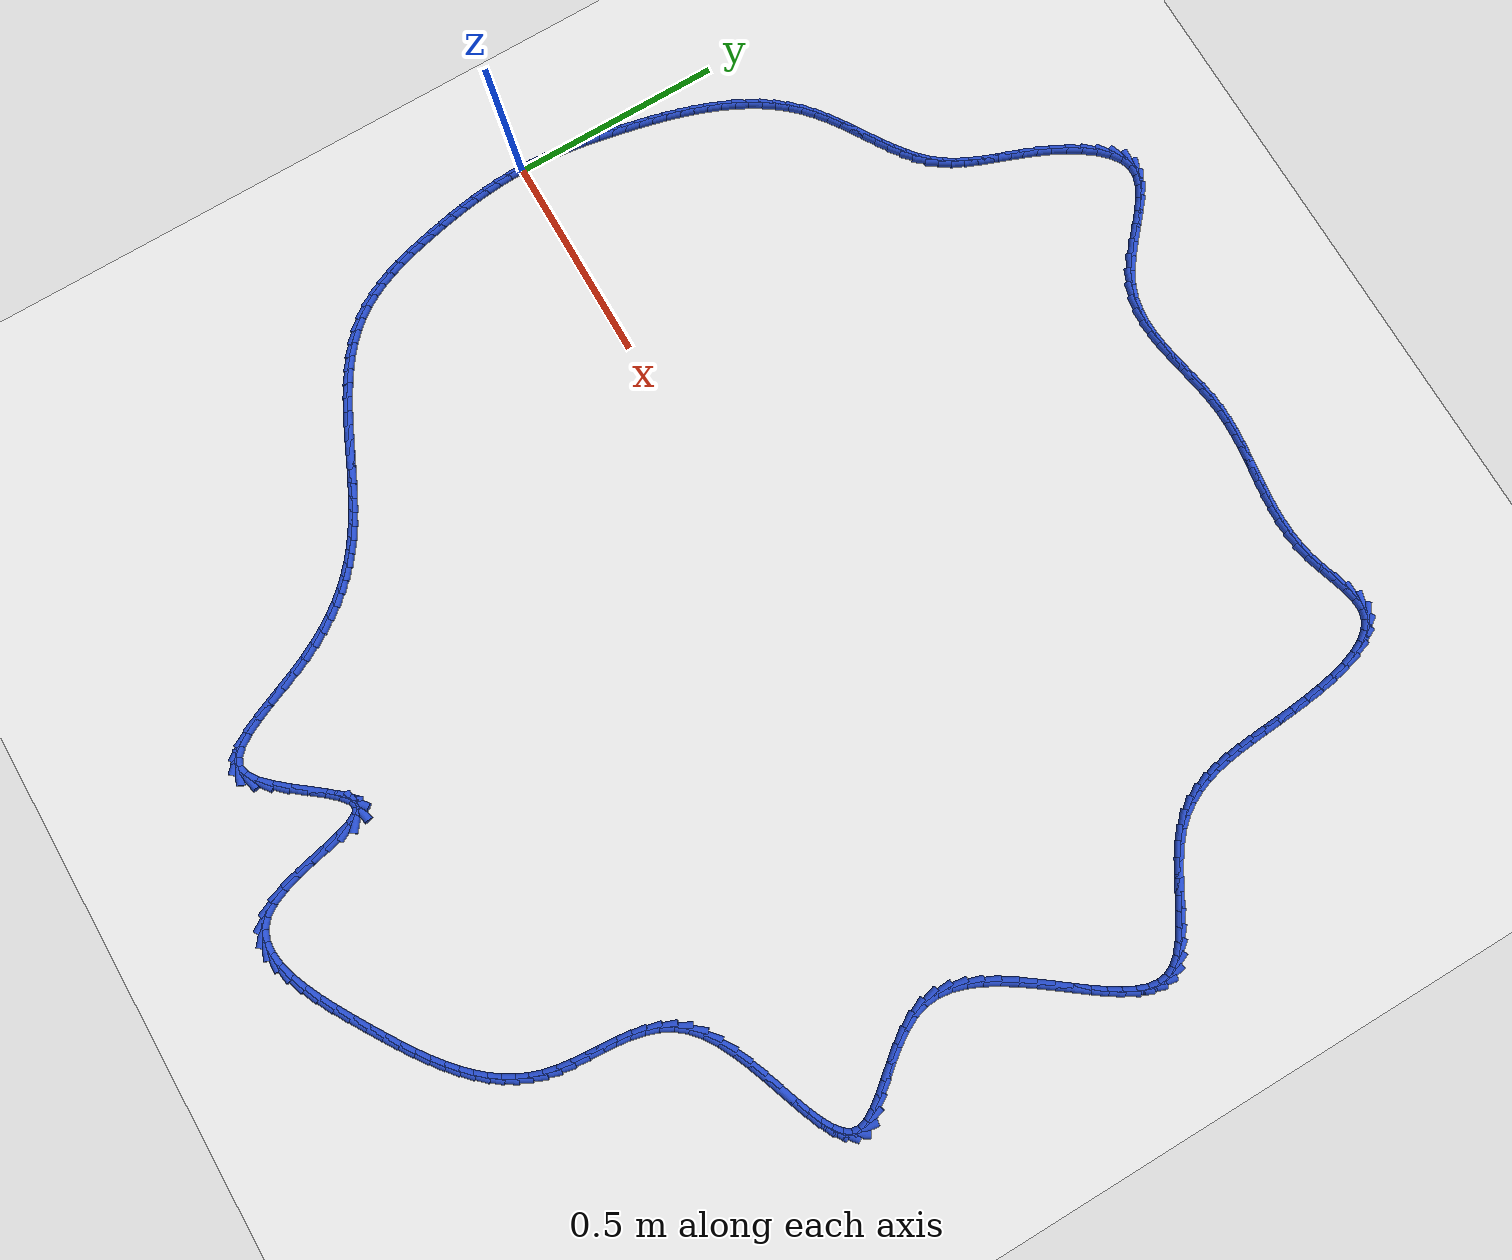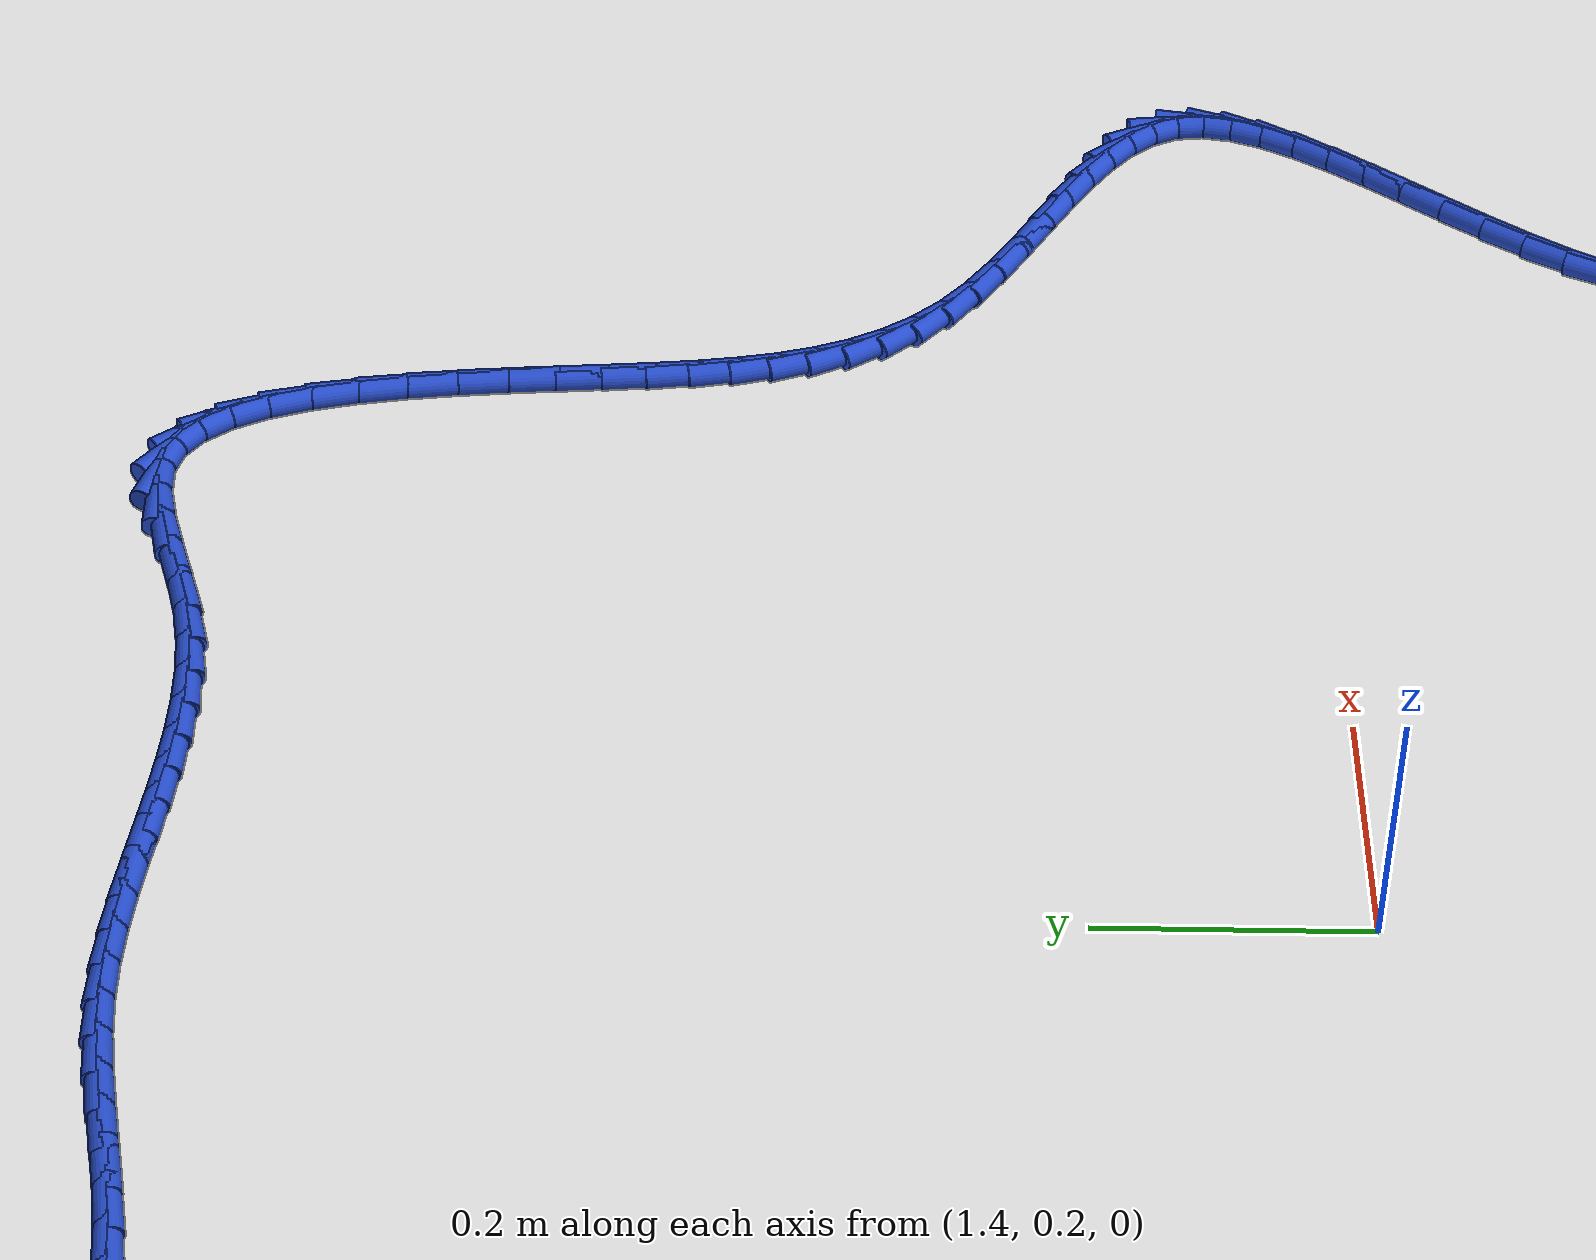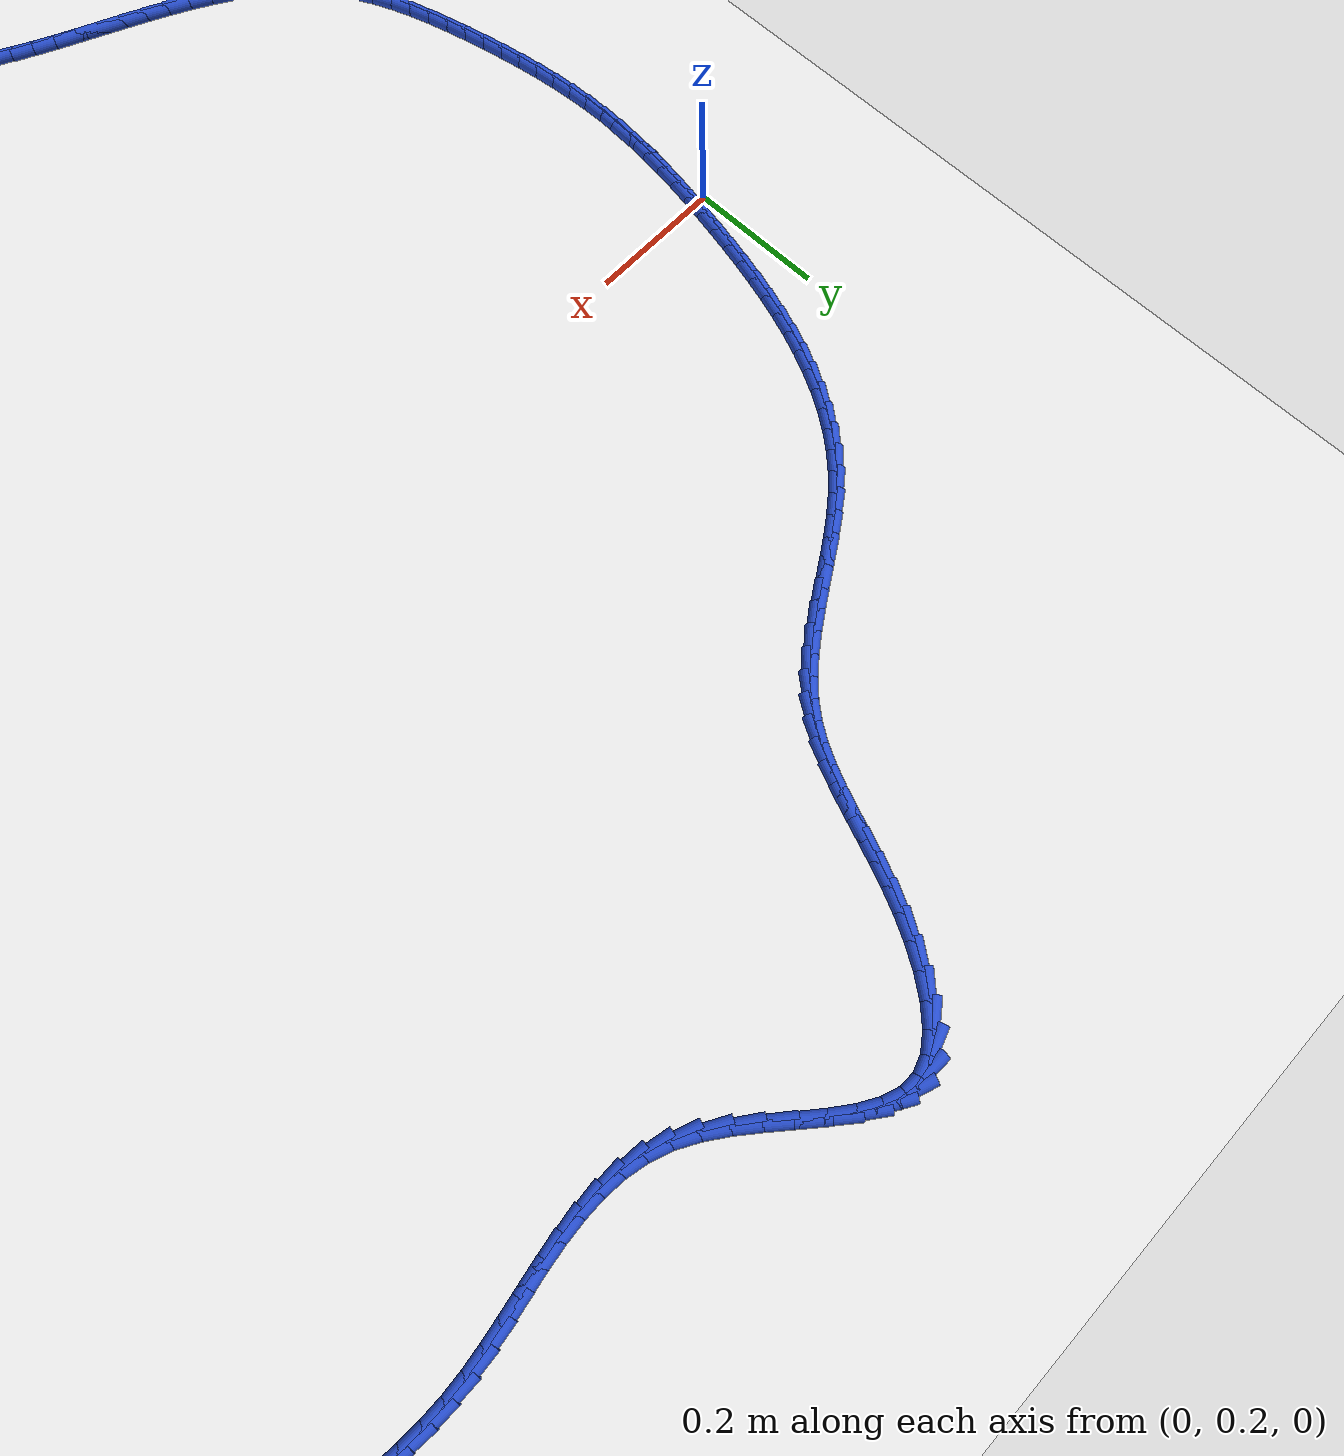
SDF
<sdf version="1.6">
 <world name="default">
  <light name="sun" type="directional">
   <pose>0 0 10 0 -0 0</pose>
   <diffuse>0.8 0.8 0.8 1</diffuse>
   <specular>0.2 0.2 0.2 1</specular>
   <attenuation>
    <range>1000</range>
    <constant>0.9</constant>
    <linear>0.01</linear>
    <quadratic>0.001</quadratic>
   </attenuation>
   <direction>-0.5 0.1 -0.9</direction>
  </light>
  <model name="ground_plane">
   <static>1</static>
   <link name="link">
    <collision name="collision">
     <geometry><plane><normal>0 0 1</normal><size>100 100</size></plane></geometry>
     <surface><friction><ode><mu>100</mu><mu2>50</mu2></ode></friction></surface>
    </collision>
    <visual name="visual">
     <cast_shadows>0</cast_shadows>
     <geometry><plane><normal>0 0 1</normal><size>100 100</size></plane></geometry>
     <material>
      <script><uri>file://media/materials/scripts/gazebo.material</uri><name>Gazebo/WhiteGlow</name></script>
     </material>
    </visual>
   </link>
  </model>
  <gravity>0 0 -9.8</gravity>
  <magnetic_field>6e-06 2.3e-05 -4.2e-05</magnetic_field>
  <atmosphere type="adiabatic"/>
  <physics name="default_physics" default="0" type="ode">
   <max_step_size>0.001</max_step_size>
   <real_time_factor>1</real_time_factor>
   <real_time_update_rate>1000</real_time_update_rate>
  </physics>
  <scene><ambient>0.4 0.4 0.4 1</ambient><background>0.7 0.7 0.7 1</background><shadows>1</shadows></scene>
  <spherical_coordinates>
   <surface_model>EARTH_WGS84</surface_model>
   <latitude_deg>0</latitude_deg>
   <longitude_deg>0</longitude_deg>
   <elevation>0</elevation>
   <heading_deg>0</heading_deg>
  </spherical_coordinates>
  <model name="line">
   <link name="link_0">
    <pose>5.204170427930421e-18 -2.7755575615628914e-17 0.01 0 1.57 1.5479271069399798</pose>
    <collision name="collision">
     <geometry><cylinder><radius>0.01</radius><length>0.08</length></cylinder></geometry>
    </collision>
    <visual name="visual">
     <material>
      <script><name>Gazebo/Blue</name><uri>file://media/materials/scripts/gazebo.material</uri></script>
     </material>
     <geometry><cylinder><radius>0.01</radius><length>0.08</length></cylinder></geometry>
    </visual>
   </link>
   <link name="link_1">
    <pose>0.0007225194036164939 0.03158802286646798 0.01 0 1.57 1.5106949477596123</pose>
    <collision name="collision">
     <geometry><cylinder><radius>0.01</radius><length>0.08</length></cylinder></geometry>
    </collision>
    <visual name="visual">
     <material>
      <script><name>Gazebo/Blue</name><uri>file://media/materials/scripts/gazebo.material</uri></script>
     </material>
     <geometry><cylinder><radius>0.01</radius><length>0.08</length></cylinder></geometry>
    </visual>
   </link>
   <link name="link_2">
    <pose>0.002623943305665586 0.0631868639454135 0.01 0 1.57 1.4771769836632676</pose>
    <collision name="collision">
     <geometry><cylinder><radius>0.01</radius><length>0.08</length></cylinder></geometry>
    </collision>
    <visual name="visual">
     <material>
      <script><name>Gazebo/Blue</name><uri>file://media/materials/scripts/gazebo.material</uri></script>
     </material>
     <geometry><cylinder><radius>0.01</radius><length>0.08</length></cylinder></geometry>
    </visual>
   </link>
   <link name="link_3">
    <pose>0.005594196453344195 0.09482103588885157 0.01 0 1.57 1.4474587203755238</pose>
    <collision name="collision">
     <geometry><cylinder><radius>0.01</radius><length>0.08</length></cylinder></geometry>
    </collision>
    <visual name="visual">
     <material>
      <script><name>Gazebo/Blue</name><uri>file://media/materials/scripts/gazebo.material</uri></script>
     </material>
     <geometry><cylinder><radius>0.01</radius><length>0.08</length></cylinder></geometry>
    </visual>
   </link>
   <link name="link_4">
    <pose>0.00952320359384925 0.12651505134879745 0.01 0 1.57 1.421570015818683</pose>
    <collision name="collision">
     <geometry><cylinder><radius>0.01</radius><length>0.08</length></cylinder></geometry>
    </collision>
    <visual name="visual">
     <material>
      <script><name>Gazebo/Blue</name><uri>file://media/materials/scripts/gazebo.material</uri></script>
     </material>
     <geometry><cylinder><radius>0.01</radius><length>0.08</length></cylinder></geometry>
    </visual>
   </link>
   <link name="link_5">
    <pose>0.014300889474377656 0.15829342297726606 0.01 0 1.57 1.3994980753813784</pose>
    <collision name="collision">
     <geometry><cylinder><radius>0.01</radius><length>0.08</length></cylinder></geometry>
    </collision>
    <visual name="visual">
     <material>
      <script><name>Gazebo/Blue</name><uri>file://media/materials/scripts/gazebo.material</uri></script>
     </material>
     <geometry><cylinder><radius>0.01</radius><length>0.08</length></cylinder></geometry>
    </visual>
   </link>
   <link name="link_6">
    <pose>0.019817178842126332 0.19018066342627266 0.01 0 1.57 1.381199406289561</pose>
    <collision name="collision">
     <geometry><cylinder><radius>0.01</radius><length>0.08</length></cylinder></geometry>
    </collision>
    <visual name="visual">
     <material>
      <script><name>Gazebo/Blue</name><uri>file://media/materials/scripts/gazebo.material</uri></script>
     </material>
     <geometry><cylinder><radius>0.01</radius><length>0.08</length></cylinder></geometry>
    </visual>
   </link>
   <link name="link_7">
    <pose>0.025961996444292208 0.22220128534783232 0.01 0 1.57 1.3666028297357178</pose>
    <collision name="collision">
     <geometry><cylinder><radius>0.01</radius><length>0.08</length></cylinder></geometry>
    </collision>
    <visual name="visual">
     <material>
      <script><name>Gazebo/Blue</name><uri>file://media/materials/scripts/gazebo.material</uri></script>
     </material>
     <geometry><cylinder><radius>0.01</radius><length>0.08</length></cylinder></geometry>
    </visual>
   </link>
   <link name="link_8">
    <pose>0.03262547887403815 0.2543796495197848 0.01 0 1.57 1.3535168513125615</pose>
    <collision name="collision">
     <geometry><cylinder><radius>0.01</radius><length>0.08</length></cylinder></geometry>
    </collision>
    <visual name="visual">
     <material>
      <script><name>Gazebo/Blue</name><uri>file://media/materials/scripts/gazebo.material</uri></script>
     </material>
     <geometry><cylinder><radius>0.01</radius><length>0.08</length></cylinder></geometry>
    </visual>
   </link>
   <link name="link_9">
    <pose>0.03975971839070129 0.28669570017577833 0.01 0 1.57 1.3368271544211339</pose>
    <collision name="collision">
     <geometry><cylinder><radius>0.01</radius><length>0.08</length></cylinder></geometry>
    </collision>
    <visual name="visual">
     <material>
      <script><name>Gazebo/Blue</name><uri>file://media/materials/scripts/gazebo.material</uri></script>
     </material>
     <geometry><cylinder><radius>0.01</radius><length>0.08</length></cylinder></geometry>
    </visual>
   </link>
   <link name="link_10">
    <pose>0.047464528884889064 0.3190234786552057 0.01 0 1.57 1.3156942760936174</pose>
    <collision name="collision">
     <geometry><cylinder><radius>0.01</radius><length>0.08</length></cylinder></geometry>
    </collision>
    <visual name="visual">
     <material>
      <script><name>Gazebo/Blue</name><uri>file://media/materials/scripts/gazebo.material</uri></script>
     </material>
     <geometry><cylinder><radius>0.01</radius><length>0.08</length></cylinder></geometry>
    </visual>
   </link>
   <link name="link_11">
    <pose>0.055861270674267806 0.35122157948058697 0.01 0 1.57 1.2899494429673124</pose>
    <collision name="collision">
     <geometry><cylinder><radius>0.01</radius><length>0.08</length></cylinder></geometry>
    </collision>
    <visual name="visual">
     <material>
      <script><name>Gazebo/Blue</name><uri>file://media/materials/scripts/gazebo.material</uri></script>
     </material>
     <geometry><cylinder><radius>0.01</radius><length>0.08</length></cylinder></geometry>
    </visual>
   </link>
   <link name="link_12">
    <pose>0.06507130407650391 0.38314859717444216 0.01 0 1.57 1.2593662667407546</pose>
    <collision name="collision">
     <geometry><cylinder><radius>0.01</radius><length>0.08</length></cylinder></geometry>
    </collision>
    <visual name="visual">
     <material>
      <script><name>Gazebo/Blue</name><uri>file://media/materials/scripts/gazebo.material</uri></script>
     </material>
     <geometry><cylinder><radius>0.01</radius><length>0.08</length></cylinder></geometry>
    </visual>
   </link>
   <link name="link_13">
    <pose>0.07521598940926373 0.41466312625929125 0.01 0 1.57 1.2236727436091208</pose>
    <collision name="collision">
     <geometry><cylinder><radius>0.01</radius><length>0.08</length></cylinder></geometry>
    </collision>
    <visual name="visual">
     <material>
      <script><name>Gazebo/Blue</name><uri>file://media/materials/scripts/gazebo.material</uri></script>
     </material>
     <geometry><cylinder><radius>0.01</radius><length>0.08</length></cylinder></geometry>
    </visual>
   </link>
   <link name="link_14">
    <pose>0.08641668699021357 0.4456237612576542 0.01 0 1.57 1.1825682829040605</pose>
    <collision name="collision">
     <geometry><cylinder><radius>0.01</radius><length>0.08</length></cylinder></geometry>
    </collision>
    <visual name="visual">
     <material>
      <script><name>Gazebo/Blue</name><uri>file://media/materials/scripts/gazebo.material</uri></script>
     </material>
     <geometry><cylinder><radius>0.01</radius><length>0.08</length></cylinder></geometry>
    </visual>
   </link>
   <link name="link_15">
    <pose>0.09879475713701985 0.47588909669205104 0.01 0 1.57 1.1357485016548954</pose>
    <collision name="collision">
     <geometry><cylinder><radius>0.01</radius><length>0.08</length></cylinder></geometry>
    </collision>
    <visual name="visual">
     <material>
      <script><name>Gazebo/Blue</name><uri>file://media/materials/scripts/gazebo.material</uri></script>
     </material>
     <geometry><cylinder><radius>0.01</radius><length>0.08</length></cylinder></geometry>
    </visual>
   </link>
   <link name="link_16">
    <pose>0.11247156016734888 0.5053177270850017 0.01 0 1.57 1.0829406344017214</pose>
    <collision name="collision">
     <geometry><cylinder><radius>0.01</radius><length>0.08</length></cylinder></geometry>
    </collision>
    <visual name="visual">
     <material>
      <script><name>Gazebo/Blue</name><uri>file://media/materials/scripts/gazebo.material</uri></script>
     </material>
     <geometry><cylinder><radius>0.01</radius><length>0.08</length></cylinder></geometry>
    </visual>
   </link>
   <link name="link_17">
    <pose>0.12756845639886707 0.5337682469590264 0.01 0 1.57 1.0239517840047918</pose>
    <collision name="collision">
     <geometry><cylinder><radius>0.01</radius><length>0.08</length></cylinder></geometry>
    </collision>
    <visual name="visual">
     <material>
      <script><name>Gazebo/Blue</name><uri>file://media/materials/scripts/gazebo.material</uri></script>
     </material>
     <geometry><cylinder><radius>0.01</radius><length>0.08</length></cylinder></geometry>
    </visual>
   </link>
   <link name="link_18">
    <pose>0.14420680614924075 0.5610992508366448 0.01 0 1.57 0.9587302216881606</pose>
    <collision name="collision">
     <geometry><cylinder><radius>0.01</radius><length>0.08</length></cylinder></geometry>
    </collision>
    <visual name="visual">
     <material>
      <script><name>Gazebo/Blue</name><uri>file://media/materials/scripts/gazebo.material</uri></script>
     </material>
     <geometry><cylinder><radius>0.01</radius><length>0.08</length></cylinder></geometry>
    </visual>
   </link>
   <link name="link_19">
    <pose>0.16250796973613624 0.5871693332403771 0.01 0 1.57 0.8874358720476883</pose>
    <collision name="collision">
     <geometry><cylinder><radius>0.01</radius><length>0.08</length></cylinder></geometry>
    </collision>
    <visual name="visual">
     <material>
      <script><name>Gazebo/Blue</name><uri>file://media/materials/scripts/gazebo.material</uri></script>
     </material>
     <geometry><cylinder><radius>0.01</radius><length>0.08</length></cylinder></geometry>
    </visual>
   </link>
   <link name="link_20">
    <pose>0.18259330747721997 0.6118370886927432 0.01 0 1.57 0.8105098833051363</pose>
    <collision name="collision">
     <geometry><cylinder><radius>0.01</radius><length>0.08</length></cylinder></geometry>
    </collision>
    <visual name="visual">
     <material>
      <script><name>Gazebo/Blue</name><uri>file://media/materials/scripts/gazebo.material</uri></script>
     </material>
     <geometry><cylinder><radius>0.01</radius><length>0.08</length></cylinder></geometry>
    </visual>
   </link>
   <link name="link_21">
    <pose>0.20458417969015824 0.6349611117162631 0.01 0 1.57 0.7293195431601147</pose>
    <collision name="collision">
     <geometry><cylinder><radius>0.01</radius><length>0.08</length></cylinder></geometry>
    </collision>
    <visual name="visual">
     <material>
      <script><name>Gazebo/Blue</name><uri>file://media/materials/scripts/gazebo.material</uri></script>
     </material>
     <geometry><cylinder><radius>0.01</radius><length>0.08</length></cylinder></geometry>
    </visual>
   </link>
   <link name="link_22">
    <pose>0.22858693797046195 0.6564122053034579 0.01 0 1.57 0.6570275330989166</pose>
    <collision name="collision">
     <geometry><cylinder><radius>0.01</radius><length>0.08</length></cylinder></geometry>
    </collision>
    <visual name="visual">
     <material>
      <script><name>Gazebo/Blue</name><uri>file://media/materials/scripts/gazebo.material</uri></script>
     </material>
     <geometry><cylinder><radius>0.01</radius><length>0.08</length></cylinder></geometry>
    </visual>
   </link>
   <link name="link_23">
    <pose>0.25439272228096554 0.6763175734729767 0.01 0 1.57 0.6047576606259017</pose>
    <collision name="collision">
     <geometry><cylinder><radius>0.01</radius><length>0.08</length></cylinder></geometry>
    </collision>
    <visual name="visual">
     <material>
      <script><name>Gazebo/Blue</name><uri>file://media/materials/scripts/gazebo.material</uri></script>
     </material>
     <geometry><cylinder><radius>0.01</radius><length>0.08</length></cylinder></geometry>
    </visual>
   </link>
   <link name="link_24">
    <pose>0.2814932727280292 0.6950479595753469 0.01 0 1.57 0.571743557279908</pose>
    <collision name="collision">
     <geometry><cylinder><radius>0.01</radius><length>0.08</length></cylinder></geometry>
    </collision>
    <visual name="visual">
     <material>
      <script><name>Gazebo/Blue</name><uri>file://media/materials/scripts/gazebo.material</uri></script>
     </material>
     <geometry><cylinder><radius>0.01</radius><length>0.08</length></cylinder></geometry>
    </visual>
   </link>
   <link name="link_25">
    <pose>0.3093684856769598 0.7129837409563066 0.01 0 1.57 0.5570754616753605</pose>
    <collision name="collision">
     <geometry><cylinder><radius>0.01</radius><length>0.08</length></cylinder></geometry>
    </collision>
    <visual name="visual">
     <material>
      <script><name>Gazebo/Blue</name><uri>file://media/materials/scripts/gazebo.material</uri></script>
     </material>
     <geometry><cylinder><radius>0.01</radius><length>0.08</length></cylinder></geometry>
    </visual>
   </link>
   <link name="link_26">
    <pose>0.3374982574930642 0.7305052949615926 0.01 0 1.57 0.5604697568227484</pose>
    <collision name="collision">
     <geometry><cylinder><radius>0.01</radius><length>0.08</length></cylinder></geometry>
    </collision>
    <visual name="visual">
     <material>
      <script><name>Gazebo/Blue</name><uri>file://media/materials/scripts/gazebo.material</uri></script>
     </material>
     <geometry><cylinder><radius>0.01</radius><length>0.08</length></cylinder></geometry>
    </visual>
   </link>
   <link name="link_27">
    <pose>0.3653624845416492 0.747992998936943 0.01 0 1.57 0.5824043736246806</pose>
    <collision name="collision">
     <geometry><cylinder><radius>0.01</radius><length>0.08</length></cylinder></geometry>
    </collision>
    <visual name="visual">
     <material>
      <script><name>Gazebo/Blue</name><uri>file://media/materials/scripts/gazebo.material</uri></script>
     </material>
     <geometry><cylinder><radius>0.01</radius><length>0.08</length></cylinder></geometry>
    </visual>
   </link>
   <link name="link_28">
    <pose>0.39244106318802163 0.7658272302280953 0.01 0 1.57 0.6241431647004706</pose>
    <collision name="collision">
     <geometry><cylinder><radius>0.01</radius><length>0.08</length></cylinder></geometry>
    </collision>
    <visual name="visual">
     <material>
      <script><name>Gazebo/Blue</name><uri>file://media/materials/scripts/gazebo.material</uri></script>
     </material>
     <geometry><cylinder><radius>0.01</radius><length>0.08</length></cylinder></geometry>
    </visual>
   </link>
   <link name="link_29">
    <pose>0.41821388979748836 0.784388366180787 0.01 0 1.57 0.6876137003023063</pose>
    <collision name="collision">
     <geometry><cylinder><radius>0.01</radius><length>0.08</length></cylinder></geometry>
    </collision>
    <visual name="visual">
     <material>
      <script><name>Gazebo/Blue</name><uri>file://media/materials/scripts/gazebo.material</uri></script>
     </material>
     <geometry><cylinder><radius>0.01</radius><length>0.08</length></cylinder></geometry>
    </visual>
   </link>
   <link name="link_30">
    <pose>0.4421608607353561 0.8040567841407555 0.01 0 1.57 0.7749924442419578</pose>
    <collision name="collision">
     <geometry><cylinder><radius>0.01</radius><length>0.08</length></cylinder></geometry>
    </collision>
    <visual name="visual">
     <material>
      <script><name>Gazebo/Blue</name><uri>file://media/materials/scripts/gazebo.material</uri></script>
     </material>
     <geometry><cylinder><radius>0.01</radius><length>0.08</length></cylinder></geometry>
    </visual>
   </link>
   <link name="link_31">
    <pose>0.4637618723669319 0.825212861453739 0.01 0 1.57 0.8862611791400495</pose>
    <collision name="collision">
     <geometry><cylinder><radius>0.01</radius><length>0.08</length></cylinder></geometry>
    </collision>
    <visual name="visual">
     <material>
      <script><name>Gazebo/Blue</name><uri>file://media/materials/scripts/gazebo.material</uri></script>
     </material>
     <geometry><cylinder><radius>0.01</radius><length>0.08</length></cylinder></geometry>
    </visual>
   </link>
   <link name="link_32">
    <pose>0.4825365131880799 0.8482156473921896 0.01 0 1.57 0.997169372033342</pose>
    <collision name="collision">
     <geometry><cylinder><radius>0.01</radius><length>0.08</length></cylinder></geometry>
    </collision>
    <visual name="visual">
     <material>
      <script><name>Gazebo/Blue</name><uri>file://media/materials/scripts/gazebo.material</uri></script>
     </material>
     <geometry><cylinder><radius>0.01</radius><length>0.08</length></cylinder></geometry>
    </visual>
   </link>
   <link name="link_33">
    <pose>0.49861254918552556 0.8730973946088532 0.01 0 1.57 1.0859136624049903</pose>
    <collision name="collision">
     <geometry><cylinder><radius>0.01</radius><length>0.08</length></cylinder></geometry>
    </collision>
    <visual name="visual">
     <material>
      <script><name>Gazebo/Blue</name><uri>file://media/materials/scripts/gazebo.material</uri></script>
     </material>
     <geometry><cylinder><radius>0.01</radius><length>0.08</length></cylinder></geometry>
    </visual>
   </link>
   <link name="link_34">
    <pose>0.5125933276794734 0.8996348080347771 0.01 0 1.57 1.1503778075862405</pose>
    <collision name="collision">
     <geometry><cylinder><radius>0.01</radius><length>0.08</length></cylinder></geometry>
    </collision>
    <visual name="visual">
     <material>
      <script><name>Gazebo/Blue</name><uri>file://media/materials/scripts/gazebo.material</uri></script>
     </material>
     <geometry><cylinder><radius>0.01</radius><length>0.08</length></cylinder></geometry>
    </visual>
   </link>
   <link name="link_35">
    <pose>0.525094865084674 0.9275977850204352 0.01 0 1.57 1.19103113966962</pose>
    <collision name="collision">
     <geometry><cylinder><radius>0.01</radius><length>0.08</length></cylinder></geometry>
    </collision>
    <visual name="visual">
     <material>
      <script><name>Gazebo/Blue</name><uri>file://media/materials/scripts/gazebo.material</uri></script>
     </material>
     <geometry><cylinder><radius>0.01</radius><length>0.08</length></cylinder></geometry>
    </visual>
   </link>
   <link name="link_36">
    <pose>0.536733177815878 0.9567562229163009 0.01 0 1.57 1.2092729480799627</pose>
    <collision name="collision">
     <geometry><cylinder><radius>0.01</radius><length>0.08</length></cylinder></geometry>
    </collision>
    <visual name="visual">
     <material>
      <script><name>Gazebo/Blue</name><uri>file://media/materials/scripts/gazebo.material</uri></script>
     </material>
     <geometry><cylinder><radius>0.01</radius><length>0.08</length></cylinder></geometry>
    </visual>
   </link>
   <link name="link_37">
    <pose>0.5481242822878362 0.9868800190728476 0.01 0 1.57 1.2067018214448675</pose>
    <collision name="collision">
     <geometry><cylinder><radius>0.01</radius><length>0.08</length></cylinder></geometry>
    </collision>
    <visual name="visual">
     <material>
      <script><name>Gazebo/Blue</name><uri>file://media/materials/scripts/gazebo.material</uri></script>
     </material>
     <geometry><cylinder><radius>0.01</radius><length>0.08</length></cylinder></geometry>
    </visual>
   </link>
   <link name="link_38">
    <pose>0.5598841949152991 1.0177390708405492 0.01 0 1.57 1.1848307651962147</pose>
    <collision name="collision">
     <geometry><cylinder><radius>0.01</radius><length>0.08</length></cylinder></geometry>
    </collision>
    <visual name="visual">
     <material>
      <script><name>Gazebo/Blue</name><uri>file://media/materials/scripts/gazebo.material</uri></script>
     </material>
     <geometry><cylinder><radius>0.01</radius><length>0.08</length></cylinder></geometry>
    </visual>
   </link>
   <link name="link_39">
    <pose>0.5726289321130176 1.0491032755698797 0.01 0 1.57 1.1451096459567947</pose>
    <collision name="collision">
     <geometry><cylinder><radius>0.01</radius><length>0.08</length></cylinder></geometry>
    </collision>
    <visual name="visual">
     <material>
      <script><name>Gazebo/Blue</name><uri>file://media/materials/scripts/gazebo.material</uri></script>
     </material>
     <geometry><cylinder><radius>0.01</radius><length>0.08</length></cylinder></geometry>
    </visual>
   </link>
   <link name="link_40">
    <pose>0.5869745102957421 1.0807425306113123 0.01 0 1.57 1.0891271212510463</pose>
    <collision name="collision">
     <geometry><cylinder><radius>0.01</radius><length>0.08</length></cylinder></geometry>
    </collision>
    <visual name="visual">
     <material>
      <script><name>Gazebo/Blue</name><uri>file://media/materials/scripts/gazebo.material</uri></script>
     </material>
     <geometry><cylinder><radius>0.01</radius><length>0.08</length></cylinder></geometry>
    </visual>
   </link>
   <link name="link_41">
    <pose>0.6035368138489531 1.1124265107854618 0.01 0 1.57 1.0186679077220195</pose>
    <collision name="collision">
     <geometry><cylinder><radius>0.01</radius><length>0.08</length></cylinder></geometry>
    </collision>
    <visual name="visual">
     <material>
      <script><name>Gazebo/Blue</name><uri>file://media/materials/scripts/gazebo.material</uri></script>
     </material>
     <geometry><cylinder><radius>0.01</radius><length>0.08</length></cylinder></geometry>
    </visual>
   </link>
   <link name="link_42">
    <pose>0.622689699532593 1.1435169633886817 0.01 0 1.57 0.9290981065030819</pose>
    <collision name="collision">
     <geometry><cylinder><radius>0.01</radius><length>0.08</length></cylinder></geometry>
    </collision>
    <visual name="visual">
     <material>
      <script><name>Gazebo/Blue</name><uri>file://media/materials/scripts/gazebo.material</uri></script>
     </material>
     <geometry><cylinder><radius>0.01</radius><length>0.08</length></cylinder></geometry>
    </visual>
   </link>
   <link name="link_43">
    <pose>0.644064093136141 1.1721234563811687 0.01 0 1.57 0.8046807505942752</pose>
    <collision name="collision">
     <geometry><cylinder><radius>0.01</radius><length>0.08</length></cylinder></geometry>
    </collision>
    <visual name="visual">
     <material>
      <script><name>Gazebo/Blue</name><uri>file://media/materials/scripts/gazebo.material</uri></script>
     </material>
     <geometry><cylinder><radius>0.01</radius><length>0.08</length></cylinder></geometry>
    </visual>
   </link>
   <link name="link_44">
    <pose>0.6671488437686505 1.1961160933711785 0.01 0 1.57 0.6176050474102868</pose>
    <collision name="collision">
     <geometry><cylinder><radius>0.01</radius><length>0.08</length></cylinder></geometry>
    </collision>
    <visual name="visual">
     <material>
      <script><name>Gazebo/Blue</name><uri>file://media/materials/scripts/gazebo.material</uri></script>
     </material>
     <geometry><cylinder><radius>0.01</radius><length>0.08</length></cylinder></geometry>
    </visual>
   </link>
   <link name="link_45">
    <pose>0.6914328005391747 1.213364977966965 0.01 0 1.57 0.32397197904822717</pose>
    <collision name="collision">
     <geometry><cylinder><radius>0.01</radius><length>0.08</length></cylinder></geometry>
    </collision>
    <visual name="visual">
     <material>
      <script><name>Gazebo/Blue</name><uri>file://media/materials/scripts/gazebo.material</uri></script>
     </material>
     <geometry><cylinder><radius>0.01</radius><length>0.08</length></cylinder></geometry>
    </visual>
   </link>
   <link name="link_46">
    <pose>0.7164063850445715 1.2217511929547278 0.01 0 1.57 -0.053096904073693475</pose>
    <collision name="collision">
     <geometry><cylinder><radius>0.01</radius><length>0.08</length></cylinder></geometry>
    </collision>
    <visual name="visual">
     <material>
      <script><name>Gazebo/Blue</name><uri>file://media/materials/scripts/gazebo.material</uri></script>
     </material>
     <geometry><cylinder><radius>0.01</radius><length>0.08</length></cylinder></geometry>
    </visual>
   </link>
   <link name="link_47">
    <pose>0.7417389103089467 1.2204048488120323 0.01 0 1.57 -0.3562527001279768</pose>
    <collision name="collision">
     <geometry><cylinder><radius>0.01</radius><length>0.08</length></cylinder></geometry>
    </collision>
    <visual name="visual">
     <material>
      <script><name>Gazebo/Blue</name><uri>file://media/materials/scripts/gazebo.material</uri></script>
     </material>
     <geometry><cylinder><radius>0.01</radius><length>0.08</length></cylinder></geometry>
    </visual>
   </link>
   <link name="link_48">
    <pose>0.767441164794041 1.2108402523085313 0.01 0 1.57 -0.5495907595236915</pose>
    <collision name="collision">
     <geometry><cylinder><radius>0.01</radius><length>0.08</length></cylinder></geometry>
    </collision>
    <visual name="visual">
     <material>
      <script><name>Gazebo/Blue</name><uri>file://media/materials/scripts/gazebo.material</uri></script>
     </material>
     <geometry><cylinder><radius>0.01</radius><length>0.08</length></cylinder></geometry>
    </visual>
   </link>
   <link name="link_49">
    <pose>0.7935623513456459 1.1948399211067307 0.01 0 1.57 -0.6604093330664472</pose>
    <collision name="collision">
     <geometry><cylinder><radius>0.01</radius><length>0.08</length></cylinder></geometry>
    </collision>
    <visual name="visual">
     <material>
      <script><name>Gazebo/Blue</name><uri>file://media/materials/scripts/gazebo.material</uri></script>
     </material>
     <geometry><cylinder><radius>0.01</radius><length>0.08</length></cylinder></geometry>
    </visual>
   </link>
   <link name="link_50">
    <pose>0.820151672809553 1.174186372869136 0.01 0 1.57 -0.7147604544904358</pose>
    <collision name="collision">
     <geometry><cylinder><radius>0.01</radius><length>0.08</length></cylinder></geometry>
    </collision>
    <visual name="visual">
     <material>
      <script><name>Gazebo/Blue</name><uri>file://media/materials/scripts/gazebo.material</uri></script>
     </material>
     <geometry><cylinder><radius>0.01</radius><length>0.08</length></cylinder></geometry>
    </visual>
   </link>
   <link name="link_51">
    <pose>0.8472583320315544 1.1506621252582538 0.01 0 1.57 -0.7269254732156176</pose>
    <collision name="collision">
     <geometry><cylinder><radius>0.01</radius><length>0.08</length></cylinder></geometry>
    </collision>
    <visual name="visual">
     <material>
      <script><name>Gazebo/Blue</name><uri>file://media/materials/scripts/gazebo.material</uri></script>
     </material>
     <geometry><cylinder><radius>0.01</radius><length>0.08</length></cylinder></geometry>
    </visual>
   </link>
   <link name="link_52">
    <pose>0.8749315318574409 1.1260496959365887 0.01 0 1.57 -0.7018714830330934</pose>
    <collision name="collision">
     <geometry><cylinder><radius>0.01</radius><length>0.08</length></cylinder></geometry>
    </collision>
    <visual name="visual">
     <material>
      <script><name>Gazebo/Blue</name><uri>file://media/materials/scripts/gazebo.material</uri></script>
     </material>
     <geometry><cylinder><radius>0.01</radius><length>0.08</length></cylinder></geometry>
    </visual>
   </link>
   <link name="link_53">
    <pose>0.9032204751330042 1.1021316025666474 0.01 0 1.57 -0.6374130631680811</pose>
    <collision name="collision">
     <geometry><cylinder><radius>0.01</radius><length>0.08</length></cylinder></geometry>
    </collision>
    <visual name="visual">
     <material>
      <script><name>Gazebo/Blue</name><uri>file://media/materials/scripts/gazebo.material</uri></script>
     </material>
     <geometry><cylinder><radius>0.01</radius><length>0.08</length></cylinder></geometry>
    </visual>
   </link>
   <link name="link_54">
    <pose>0.9321743647040365 1.0806903628109354 0.01 0 1.57 -0.5250140542140111</pose>
    <collision name="collision">
     <geometry><cylinder><radius>0.01</radius><length>0.08</length></cylinder></geometry>
    </collision>
    <visual name="visual">
     <material>
      <script><name>Gazebo/Blue</name><uri>file://media/materials/scripts/gazebo.material</uri></script>
     </material>
     <geometry><cylinder><radius>0.01</radius><length>0.08</length></cylinder></geometry>
    </visual>
   </link>
   <link name="link_55">
    <pose>0.9618422320724405 1.0635055813814802 0.01 0 1.57 -0.371762286327902</pose>
    <collision name="collision">
     <geometry><cylinder><radius>0.01</radius><length>0.08</length></cylinder></geometry>
    </collision>
    <visual name="visual">
     <material>
      <script><name>Gazebo/Blue</name><uri>file://media/materials/scripts/gazebo.material</uri></script>
     </material>
     <geometry><cylinder><radius>0.01</radius><length>0.08</length></cylinder></geometry>
    </visual>
   </link>
   <link name="link_56">
    <pose>0.9922319347975153 1.0516568808850781 0.01 0 1.57 -0.2230528186521789</pose>
    <collision name="collision">
     <geometry><cylinder><radius>0.01</radius><length>0.08</length></cylinder></geometry>
    </collision>
    <visual name="visual">
     <material>
      <script><name>Gazebo/Blue</name><uri>file://media/materials/scripts/gazebo.material</uri></script>
     </material>
     <geometry><cylinder><radius>0.01</radius><length>0.08</length></cylinder></geometry>
    </visual>
   </link>
   <link name="link_57">
    <pose>1.0232569620585044 1.0446195639834082 0.01 0 1.57 -0.09396820062387937</pose>
    <collision name="collision">
     <geometry><cylinder><radius>0.01</radius><length>0.08</length></cylinder></geometry>
    </collision>
    <visual name="visual">
     <material>
      <script><name>Gazebo/Blue</name><uri>file://media/materials/scripts/gazebo.material</uri></script>
     </material>
     <geometry><cylinder><radius>0.01</radius><length>0.08</length></cylinder></geometry>
    </visual>
   </link>
   <link name="link_58">
    <pose>1.054817637082614 1.0416451041335186 0.01 0 1.57 0.010621671949531354</pose>
    <collision name="collision">
     <geometry><cylinder><radius>0.01</radius><length>0.08</length></cylinder></geometry>
    </collision>
    <visual name="visual">
     <material>
      <script><name>Gazebo/Blue</name><uri>file://media/materials/scripts/gazebo.material</uri></script>
     </material>
     <geometry><cylinder><radius>0.01</radius><length>0.08</length></cylinder></geometry>
    </visual>
   </link>
   <link name="link_59">
    <pose>1.0868142830970495 1.0419849747924583 0.01 0 1.57 0.0896265568161383</pose>
    <collision name="collision">
     <geometry><cylinder><radius>0.01</radius><length>0.08</length></cylinder></geometry>
    </collision>
    <visual name="visual">
     <material>
      <script><name>Gazebo/Blue</name><uri>file://media/materials/scripts/gazebo.material</uri></script>
     </material>
     <geometry><cylinder><radius>0.01</radius><length>0.08</length></cylinder></geometry>
    </visual>
   </link>
   <link name="link_60">
    <pose>1.1191472233290178 1.044890649417276 0.01 0 1.57 0.1440074333277709</pose>
    <collision name="collision">
     <geometry><cylinder><radius>0.01</radius><length>0.08</length></cylinder></geometry>
    </collision>
    <visual name="visual">
     <material>
      <script><name>Gazebo/Blue</name><uri>file://media/materials/scripts/gazebo.material</uri></script>
     </material>
     <geometry><cylinder><radius>0.01</radius><length>0.08</length></cylinder></geometry>
    </visual>
   </link>
   <link name="link_61">
    <pose>1.1517167810057243 1.0496136014650201 0.01 0 1.57 0.17526421718419646</pose>
    <collision name="collision">
     <geometry><cylinder><radius>0.01</radius><length>0.08</length></cylinder></geometry>
    </collision>
    <visual name="visual">
     <material>
      <script><name>Gazebo/Blue</name><uri>file://media/materials/scripts/gazebo.material</uri></script>
     </material>
     <geometry><cylinder><radius>0.01</radius><length>0.08</length></cylinder></geometry>
    </visual>
   </link>
   <link name="link_62">
    <pose>1.1844232793543754 1.0554053043927392 0.01 0 1.57 0.1845356645171906</pose>
    <collision name="collision">
     <geometry><cylinder><radius>0.01</radius><length>0.08</length></cylinder></geometry>
    </collision>
    <visual name="visual">
     <material>
      <script><name>Gazebo/Blue</name><uri>file://media/materials/scripts/gazebo.material</uri></script>
     </material>
     <geometry><cylinder><radius>0.01</radius><length>0.08</length></cylinder></geometry>
    </visual>
   </link>
   <link name="link_63">
    <pose>1.2171670416021767 1.0615172316574815 0.01 0 1.57 0.17218820459338285</pose>
    <collision name="collision">
     <geometry><cylinder><radius>0.01</radius><length>0.08</length></cylinder></geometry>
    </collision>
    <visual name="visual">
     <material>
      <script><name>Gazebo/Blue</name><uri>file://media/materials/scripts/gazebo.material</uri></script>
     </material>
     <geometry><cylinder><radius>0.01</radius><length>0.08</length></cylinder></geometry>
    </visual>
   </link>
   <link name="link_64">
    <pose>1.2498483909763347 1.067200856716296 0.01 0 1.57 0.13771133423715542</pose>
    <collision name="collision">
     <geometry><cylinder><radius>0.01</radius><length>0.08</length></cylinder></geometry>
    </collision>
    <visual name="visual">
     <material>
      <script><name>Gazebo/Blue</name><uri>file://media/materials/scripts/gazebo.material</uri></script>
     </material>
     <geometry><cylinder><radius>0.01</radius><length>0.08</length></cylinder></geometry>
    </visual>
   </link>
   <link name="link_65">
    <pose>1.2823676507040551 1.0717076530262313 0.01 0 1.57 0.07998828589498423</pose>
    <collision name="collision">
     <geometry><cylinder><radius>0.01</radius><length>0.08</length></cylinder></geometry>
    </collision>
    <visual name="visual">
     <material>
      <script><name>Gazebo/Blue</name><uri>file://media/materials/scripts/gazebo.material</uri></script>
     </material>
     <geometry><cylinder><radius>0.01</radius><length>0.08</length></cylinder></geometry>
    </visual>
   </link>
   <link name="link_66">
    <pose>1.314625760937037 1.0742934410561151 0.01 0 1.57 0.010227394941470406</pose>
    <collision name="collision">
     <geometry><cylinder><radius>0.01</radius><length>0.08</length></cylinder></geometry>
    </collision>
    <visual name="visual">
     <material>
      <script><name>Gazebo/Blue</name><uri>file://media/materials/scripts/gazebo.material</uri></script>
     </material>
     <geometry><cylinder><radius>0.01</radius><length>0.08</length></cylinder></geometry>
    </visual>
   </link>
   <link name="link_67">
    <pose>1.3465813141288823 1.0746202745148112 0.01 0 1.57 -0.0484710967883992</pose>
    <collision name="collision">
     <geometry><cylinder><radius>0.01</radius><length>0.08</length></cylinder></geometry>
    </collision>
    <visual name="visual">
     <material>
      <script><name>Gazebo/Blue</name><uri>file://media/materials/scripts/gazebo.material</uri></script>
     </material>
     <geometry><cylinder><radius>0.01</radius><length>0.08</length></cylinder></geometry>
    </visual>
   </link>
   <link name="link_68">
    <pose>1.378296728196593 1.0730817885572372 0.01 0 1.57 -0.09272041802726982</pose>
    <collision name="collision">
     <geometry><cylinder><radius>0.01</radius><length>0.08</length></cylinder></geometry>
    </collision>
    <visual name="visual">
     <material>
      <script><name>Gazebo/Blue</name><uri>file://media/materials/scripts/gazebo.material</uri></script>
     </material>
     <geometry><cylinder><radius>0.01</radius><length>0.08</length></cylinder></geometry>
    </visual>
   </link>
   <link name="link_69">
    <pose>1.4098452868233216 1.0701481813764424 0.01 0 1.57 -0.12205852579412695</pose>
    <collision name="collision">
     <geometry><cylinder><radius>0.01</radius><length>0.08</length></cylinder></geometry>
    </collision>
    <visual name="visual">
     <material>
      <script><name>Gazebo/Blue</name><uri>file://media/materials/scripts/gazebo.material</uri></script>
     </material>
     <geometry><cylinder><radius>0.01</radius><length>0.08</length></cylinder></geometry>
    </visual>
   </link>
   <link name="link_70">
    <pose>1.441300273692222 1.066289651165478 0.01 0 1.57 -0.1363616556768697</pose>
    <collision name="collision">
     <geometry><cylinder><radius>0.01</radius><length>0.08</length></cylinder></geometry>
    </collision>
    <visual name="visual">
     <material>
      <script><name>Gazebo/Blue</name><uri>file://media/materials/scripts/gazebo.material</uri></script>
     </material>
     <geometry><cylinder><radius>0.01</radius><length>0.08</length></cylinder></geometry>
    </visual>
   </link>
   <link name="link_71">
    <pose>1.472734972486446 1.0619763961173934 0.01 0 1.57 -0.13565258812657902</pose>
    <collision name="collision">
     <geometry><cylinder><radius>0.01</radius><length>0.08</length></cylinder></geometry>
    </collision>
    <visual name="visual">
     <material>
      <script><name>Gazebo/Blue</name><uri>file://media/materials/scripts/gazebo.material</uri></script>
     </material>
     <geometry><cylinder><radius>0.01</radius><length>0.08</length></cylinder></geometry>
    </visual>
   </link>
   <link name="link_72">
    <pose>1.5042226668891485 1.0576786144252386 0.01 0 1.57 -0.12000368366399121</pose>
    <collision name="collision">
     <geometry><cylinder><radius>0.01</radius><length>0.08</length></cylinder></geometry>
    </collision>
    <visual name="visual">
     <material>
      <script><name>Gazebo/Blue</name><uri>file://media/materials/scripts/gazebo.material</uri></script>
     </material>
     <geometry><cylinder><radius>0.01</radius><length>0.08</length></cylinder></geometry>
    </visual>
   </link>
   <link name="link_73">
    <pose>1.535836640583481 1.0538665042820645 0.01 0 1.57 -0.08954059487010384</pose>
    <collision name="collision">
     <geometry><cylinder><radius>0.01</radius><length>0.08</length></cylinder></geometry>
    </collision>
    <visual name="visual">
     <material>
      <script><name>Gazebo/Blue</name><uri>file://media/materials/scripts/gazebo.material</uri></script>
     </material>
     <geometry><cylinder><radius>0.01</radius><length>0.08</length></cylinder></geometry>
    </visual>
   </link>
   <link name="link_74">
    <pose>1.5676501772525977 1.0510102638809204 0.01 0 1.57 -0.04454308435029531</pose>
    <collision name="collision">
     <geometry><cylinder><radius>0.01</radius><length>0.08</length></cylinder></geometry>
    </collision>
    <visual name="visual">
     <material>
      <script><name>Gazebo/Blue</name><uri>file://media/materials/scripts/gazebo.material</uri></script>
     </material>
     <geometry><cylinder><radius>0.01</radius><length>0.08</length></cylinder></geometry>
    </visual>
   </link>
   <link name="link_75">
    <pose>1.599736560579651 1.0495800914148568 0.01 0 1.57 0.014370196008240849</pose>
    <collision name="collision">
     <geometry><cylinder><radius>0.01</radius><length>0.08</length></cylinder></geometry>
    </collision>
    <visual name="visual">
     <material>
      <script><name>Gazebo/Blue</name><uri>file://media/materials/scripts/gazebo.material</uri></script>
     </material>
     <geometry><cylinder><radius>0.01</radius><length>0.08</length></cylinder></geometry>
    </visual>
   </link>
   <link name="link_76">
    <pose>1.6321690742477937 1.0500461850769236 0.01 0 1.57 0.08600925522141821</pose>
    <collision name="collision">
     <geometry><cylinder><radius>0.01</radius><length>0.08</length></cylinder></geometry>
    </collision>
    <visual name="visual">
     <material>
      <script><name>Gazebo/Blue</name><uri>file://media/materials/scripts/gazebo.material</uri></script>
     </material>
     <geometry><cylinder><radius>0.01</radius><length>0.08</length></cylinder></geometry>
    </visual>
   </link>
   <link name="link_77">
    <pose>1.6650210019401799 1.0528787430601712 0.01 0 1.57 0.16840864182320414</pose>
    <collision name="collision">
     <geometry><cylinder><radius>0.01</radius><length>0.08</length></cylinder></geometry>
    </collision>
    <visual name="visual">
     <material>
      <script><name>Gazebo/Blue</name><uri>file://media/materials/scripts/gazebo.material</uri></script>
     </material>
     <geometry><cylinder><radius>0.01</radius><length>0.08</length></cylinder></geometry>
    </visual>
   </link>
   <link name="link_78">
    <pose>1.698365627339962 1.0585479635576496 0.01 0 1.57 0.2545476252437074</pose>
    <collision name="collision">
     <geometry><cylinder><radius>0.01</radius><length>0.08</length></cylinder></geometry>
    </collision>
    <visual name="visual">
     <material>
      <script><name>Gazebo/Blue</name><uri>file://media/materials/scripts/gazebo.material</uri></script>
     </material>
     <geometry><cylinder><radius>0.01</radius><length>0.08</length></cylinder></geometry>
    </visual>
   </link>
   <link name="link_79">
    <pose>1.7322175355558753 1.0673559495904146 0.01 0 1.57 0.3014308451783119</pose>
    <collision name="collision">
     <geometry><cylinder><radius>0.01</radius><length>0.08</length></cylinder></geometry>
    </collision>
    <visual name="visual">
     <material>
      <script><name>Gazebo/Blue</name><uri>file://media/materials/scripts/gazebo.material</uri></script>
     </material>
     <geometry><cylinder><radius>0.01</radius><length>0.08</length></cylinder></geometry>
    </visual>
   </link>
   <link name="link_80">
    <pose>1.7659794784044798 1.0778526965091089 0.01 0 1.57 0.288111645964463</pose>
    <collision name="collision">
     <geometry><cylinder><radius>0.01</radius><length>0.08</length></cylinder></geometry>
    </collision>
    <visual name="visual">
     <material>
      <script><name>Gazebo/Blue</name><uri>file://media/materials/scripts/gazebo.material</uri></script>
     </material>
     <geometry><cylinder><radius>0.01</radius><length>0.08</length></cylinder></geometry>
    </visual>
   </link>
   <link name="link_81">
    <pose>1.798690578401799 1.087546874037273 0.01 0 1.57 0.20513981655084135</pose>
    <collision name="collision">
     <geometry><cylinder><radius>0.01</radius><length>0.08</length></cylinder></geometry>
    </collision>
    <visual name="visual">
     <material>
      <script><name>Gazebo/Blue</name><uri>file://media/materials/scripts/gazebo.material</uri></script>
     </material>
     <geometry><cylinder><radius>0.01</radius><length>0.08</length></cylinder></geometry>
    </visual>
   </link>
   <link name="link_82">
    <pose>1.8293851532663985 1.0939333923946895 0.01 0 1.57 0.02070149516500042</pose>
    <collision name="collision">
     <geometry><cylinder><radius>0.01</radius><length>0.08</length></cylinder></geometry>
    </collision>
    <visual name="visual">
     <material>
      <script><name>Gazebo/Blue</name><uri>file://media/materials/scripts/gazebo.material</uri></script>
     </material>
     <geometry><cylinder><radius>0.01</radius><length>0.08</length></cylinder></geometry>
    </visual>
   </link>
   <link name="link_83">
    <pose>1.8570975207168425 1.0945071618011408 0.01 0 1.57 -0.30284562523795694</pose>
    <collision name="collision">
     <geometry><cylinder><radius>0.01</radius><length>0.08</length></cylinder></geometry>
    </collision>
    <visual name="visual">
     <material>
      <script><name>Gazebo/Blue</name><uri>file://media/materials/scripts/gazebo.material</uri></script>
     </material>
     <geometry><cylinder><radius>0.01</radius><length>0.08</length></cylinder></geometry>
    </visual>
   </link>
   <link name="link_84">
    <pose>1.8809682199243507 1.087048596527883 0.01 0 1.57 -0.6574080307313552</pose>
    <collision name="collision">
     <geometry><cylinder><radius>0.01</radius><length>0.08</length></cylinder></geometry>
    </collision>
    <visual name="visual">
     <material>
      <script><name>Gazebo/Blue</name><uri>file://media/materials/scripts/gazebo.material</uri></script>
     </material>
     <geometry><cylinder><radius>0.01</radius><length>0.08</length></cylinder></geometry>
    </visual>
   </link>
   <link name="link_85">
    <pose>1.9009795616434255 1.0716006406029694 0.01 0 1.57 -0.9331448604624866</pose>
    <collision name="collision">
     <geometry><cylinder><radius>0.01</radius><length>0.08</length></cylinder></geometry>
    </collision>
    <visual name="visual">
     <material>
      <script><name>Gazebo/Blue</name><uri>file://media/materials/scripts/gazebo.material</uri></script>
     </material>
     <geometry><cylinder><radius>0.01</radius><length>0.08</length></cylinder></geometry>
    </visual>
   </link>
   <link name="link_86">
    <pose>1.9175145420305069 1.049283207939171 0.01 0 1.57 -1.1239987708524335</pose>
    <collision name="collision">
     <geometry><cylinder><radius>0.01</radius><length>0.08</length></cylinder></geometry>
    </collision>
    <visual name="visual">
     <material>
      <script><name>Gazebo/Blue</name><uri>file://media/materials/scripts/gazebo.material</uri></script>
     </material>
     <geometry><cylinder><radius>0.01</radius><length>0.08</length></cylinder></geometry>
    </visual>
   </link>
   <link name="link_87">
    <pose>1.930958606579573 1.021222795825519 0.01 0 1.57 -1.2532851027462428</pose>
    <collision name="collision">
     <geometry><cylinder><radius>0.01</radius><length>0.08</length></cylinder></geometry>
    </collision>
    <visual name="visual">
     <material>
      <script><name>Gazebo/Blue</name><uri>file://media/materials/scripts/gazebo.material</uri></script>
     </material>
     <geometry><cylinder><radius>0.01</radius><length>0.08</length></cylinder></geometry>
    </visual>
   </link>
   <link name="link_88">
    <pose>1.9416972007846 0.9885459015510446 0.01 0 1.57 -1.3420985782314852</pose>
    <collision name="collision">
     <geometry><cylinder><radius>0.01</radius><length>0.08</length></cylinder></geometry>
    </collision>
    <visual name="visual">
     <material>
      <script><name>Gazebo/Blue</name><uri>file://media/materials/scripts/gazebo.material</uri></script>
     </material>
     <geometry><cylinder><radius>0.01</radius><length>0.08</length></cylinder></geometry>
    </visual>
   </link>
   <link name="link_89">
    <pose>1.9501157701395662 0.9523790224047783 0.01 0 1.57 -1.4040758105081967</pose>
    <collision name="collision">
     <geometry><cylinder><radius>0.01</radius><length>0.08</length></cylinder></geometry>
    </collision>
    <visual name="visual">
     <material>
      <script><name>Gazebo/Blue</name><uri>file://media/materials/scripts/gazebo.material</uri></script>
     </material>
     <geometry><cylinder><radius>0.01</radius><length>0.08</length></cylinder></geometry>
    </visual>
   </link>
   <link name="link_90">
    <pose>1.9565997601384482 0.9138486556757519 0.01 0 1.57 -1.447334341616804</pose>
    <collision name="collision">
     <geometry><cylinder><radius>0.01</radius><length>0.08</length></cylinder></geometry>
    </collision>
    <visual name="visual">
     <material>
      <script><name>Gazebo/Blue</name><uri>file://media/materials/scripts/gazebo.material</uri></script>
     </material>
     <geometry><cylinder><radius>0.01</radius><length>0.08</length></cylinder></geometry>
    </visual>
   </link>
   <link name="link_91">
    <pose>1.9615346162752223 0.8740812986529958 0.01 0 1.57 -1.4765087529756196</pose>
    <collision name="collision">
     <geometry><cylinder><radius>0.01</radius><length>0.08</length></cylinder></geometry>
    </collision>
    <visual name="visual">
     <material>
      <script><name>Gazebo/Blue</name><uri>file://media/materials/scripts/gazebo.material</uri></script>
     </material>
     <geometry><cylinder><radius>0.01</radius><length>0.08</length></cylinder></geometry>
    </visual>
   </link>
   <link name="link_92">
    <pose>1.9653057840438655 0.8342034486255412 0.01 0 1.57 -1.4939409872384355</pose>
    <collision name="collision">
     <geometry><cylinder><radius>0.01</radius><length>0.08</length></cylinder></geometry>
    </collision>
    <visual name="visual">
     <material>
      <script><name>Gazebo/Blue</name><uri>file://media/materials/scripts/gazebo.material</uri></script>
     </material>
     <geometry><cylinder><radius>0.01</radius><length>0.08</length></cylinder></geometry>
    </visual>
   </link>
   <link name="link_93">
    <pose>1.968301474854559 0.79530191952927 0.01 0 1.57 -1.500124668350733</pose>
    <collision name="collision">
     <geometry><cylinder><radius>0.01</radius><length>0.08</length></cylinder></geometry>
    </collision>
    <visual name="visual">
     <material>
      <script><name>Gazebo/Blue</name><uri>file://media/materials/scripts/gazebo.material</uri></script>
     </material>
     <geometry><cylinder><radius>0.01</radius><length>0.08</length></cylinder></geometry>
    </visual>
   </link>
   <link name="link_94">
    <pose>1.9709515903632617 0.7578653839884442 0.01 0 1.57 -1.493978853736317</pose>
    <collision name="collision">
     <geometry><cylinder><radius>0.01</radius><length>0.08</length></cylinder></geometry>
    </collision>
    <visual name="visual">
     <material>
      <script><name>Gazebo/Blue</name><uri>file://media/materials/scripts/gazebo.material</uri></script>
     </material>
     <geometry><cylinder><radius>0.01</radius><length>0.08</length></cylinder></geometry>
    </visual>
   </link>
   <link name="link_95">
    <pose>1.9737182816250836 0.7219198237136903 0.01 0 1.57 -1.4739402076145902</pose>
    <collision name="collision">
     <geometry><cylinder><radius>0.01</radius><length>0.08</length></cylinder></geometry>
    </collision>
    <visual name="visual">
     <material>
      <script><name>Gazebo/Blue</name><uri>file://media/materials/scripts/gazebo.material</uri></script>
     </material>
     <geometry><cylinder><radius>0.01</radius><length>0.08</length></cylinder></geometry>
    </visual>
   </link>
   <link name="link_96">
    <pose>1.977064538332379 0.6874791882586834 0.01 0 1.57 -1.4382673659171128</pose>
    <collision name="collision">
     <geometry><cylinder><radius>0.01</radius><length>0.08</length></cylinder></geometry>
    </collision>
    <visual name="visual">
     <material>
      <script><name>Gazebo/Blue</name><uri>file://media/materials/scripts/gazebo.material</uri></script>
     </material>
     <geometry><cylinder><radius>0.01</radius><length>0.08</length></cylinder></geometry>
    </visual>
   </link>
   <link name="link_97">
    <pose>1.9814533501775022 0.6545574271770981 0.01 0 1.57 -1.3851735284225686</pose>
    <collision name="collision">
     <geometry><cylinder><radius>0.01</radius><length>0.08</length></cylinder></geometry>
    </collision>
    <visual name="visual">
     <material>
      <script><name>Gazebo/Blue</name><uri>file://media/materials/scripts/gazebo.material</uri></script>
     </material>
     <geometry><cylinder><radius>0.01</radius><length>0.08</length></cylinder></geometry>
    </visual>
   </link>
   <link name="link_98">
    <pose>1.987347706852808 0.6231684900226095 0.01 0 1.57 -1.3131689508341493</pose>
    <collision name="collision">
     <geometry><cylinder><radius>0.01</radius><length>0.08</length></cylinder></geometry>
    </collision>
    <visual name="visual">
     <material>
      <script><name>Gazebo/Blue</name><uri>file://media/materials/scripts/gazebo.material</uri></script>
     </material>
     <geometry><cylinder><radius>0.01</radius><length>0.08</length></cylinder></geometry>
    </visual>
   </link>
   <link name="link_99">
    <pose>1.99521059805065 0.5933263263488924 0.01 0 1.57 -1.2217050976580177</pose>
    <collision name="collision">
     <geometry><cylinder><radius>0.01</radius><length>0.08</length></cylinder></geometry>
    </collision>
    <visual name="visual">
     <material>
      <script><name>Gazebo/Blue</name><uri>file://media/materials/scripts/gazebo.material</uri></script>
     </material>
     <geometry><cylinder><radius>0.01</radius><length>0.08</length></cylinder></geometry>
    </visual>
   </link>
   <link name="link_100">
    <pose>2.0055050134633823 0.5650448857096215 0.01 0 1.57 -1.112087074585562</pose>
    <collision name="collision">
     <geometry><cylinder><radius>0.01</radius><length>0.08</length></cylinder></geometry>
    </collision>
    <visual name="visual">
     <material>
      <script><name>Gazebo/Blue</name><uri>file://media/materials/scripts/gazebo.material</uri></script>
     </material>
     <geometry><cylinder><radius>0.01</radius><length>0.08</length></cylinder></geometry>
    </visual>
   </link>
   <link name="link_101">
    <pose>2.0186939427833592 0.5383381176584715 0.01 0 1.57 -0.9882985814596701</pose>
    <collision name="collision">
     <geometry><cylinder><radius>0.01</radius><length>0.08</length></cylinder></geometry>
    </collision>
    <visual name="visual">
     <material>
      <script><name>Gazebo/Blue</name><uri>file://media/materials/scripts/gazebo.material</uri></script>
     </material>
     <geometry><cylinder><radius>0.01</radius><length>0.08</length></cylinder></geometry>
    </visual>
   </link>
   <link name="link_102">
    <pose>2.0352403757029354 0.5132199717491175 0.01 0 1.57 -0.8570271997223394</pose>
    <collision name="collision">
     <geometry><cylinder><radius>0.01</radius><length>0.08</length></cylinder></geometry>
    </collision>
    <visual name="visual">
     <material>
      <script><name>Gazebo/Blue</name><uri>file://media/materials/scripts/gazebo.material</uri></script>
     </material>
     <geometry><cylinder><radius>0.01</radius><length>0.08</length></cylinder></geometry>
    </visual>
   </link>
   <link name="link_103">
    <pose>2.055607301914464 0.4897043975352341 0.01 0 1.57 -0.7295971118241893</pose>
    <collision name="collision">
     <geometry><cylinder><radius>0.01</radius><length>0.08</length></cylinder></geometry>
    </collision>
    <visual name="visual">
     <material>
      <script><name>Gazebo/Blue</name><uri>file://media/materials/scripts/gazebo.material</uri></script>
     </material>
     <geometry><cylinder><radius>0.01</radius><length>0.08</length></cylinder></geometry>
    </visual>
   </link>
   <link name="link_104">
    <pose>2.0801269045937816 0.46777915912810747 0.01 0 1.57 -0.634532130063444</pose>
    <collision name="collision">
     <geometry><cylinder><radius>0.01</radius><length>0.08</length></cylinder></geometry>
    </collision>
    <visual name="visual">
     <material>
      <script><name>Gazebo/Blue</name><uri>file://media/materials/scripts/gazebo.material</uri></script>
     </material>
     <geometry><cylinder><radius>0.01</radius><length>0.08</length></cylinder></geometry>
    </visual>
   </link>
   <link name="link_105">
    <pose>2.108060681411876 0.4472176859533394 0.01 0 1.57 -0.5757550613218255</pose>
    <collision name="collision">
     <geometry><cylinder><radius>0.01</radius><length>0.08</length></cylinder></geometry>
    </collision>
    <visual name="visual">
     <material>
      <script><name>Gazebo/Blue</name><uri>file://media/materials/scripts/gazebo.material</uri></script>
     </material>
     <geometry><cylinder><radius>0.01</radius><length>0.08</length></cylinder></geometry>
    </visual>
   </link>
   <link name="link_106">
    <pose>2.1381463226619006 0.42768854929734806 0.01 0 1.57 -0.5462385934227894</pose>
    <collision name="collision">
     <geometry><cylinder><radius>0.01</radius><length>0.08</length></cylinder></geometry>
    </collision>
    <visual name="visual">
     <material>
      <script><name>Gazebo/Blue</name><uri>file://media/materials/scripts/gazebo.material</uri></script>
     </material>
     <geometry><cylinder><radius>0.01</radius><length>0.08</length></cylinder></geometry>
    </visual>
   </link>
   <link name="link_107">
    <pose>2.1691179460862138 0.4088596052771137 0.01 0 1.57 -0.5429600679326003</pose>
    <collision name="collision">
     <geometry><cylinder><radius>0.01</radius><length>0.08</length></cylinder></geometry>
    </collision>
    <visual name="visual">
     <material>
      <script><name>Gazebo/Blue</name><uri>file://media/materials/scripts/gazebo.material</uri></script>
     </material>
     <geometry><cylinder><radius>0.01</radius><length>0.08</length></cylinder></geometry>
    </visual>
   </link>
   <link name="link_108">
    <pose>2.1997096694271723 0.39039871000961607 0.01 0 1.57 -0.5668483720270161</pose>
    <collision name="collision">
     <geometry><cylinder><radius>0.01</radius><length>0.08</length></cylinder></geometry>
    </collision>
    <visual name="visual">
     <material>
      <script><name>Gazebo/Blue</name><uri>file://media/materials/scripts/gazebo.material</uri></script>
     </material>
     <geometry><cylinder><radius>0.01</radius><length>0.08</length></cylinder></geometry>
    </visual>
   </link>
   <link name="link_109">
    <pose>2.228655610427135 0.3719737196118356 0.01 0 1.57 -0.623429596093039</pose>
    <collision name="collision">
     <geometry><cylinder><radius>0.01</radius><length>0.08</length></cylinder></geometry>
    </collision>
    <visual name="visual">
     <material>
      <script><name>Gazebo/Blue</name><uri>file://media/materials/scripts/gazebo.material</uri></script>
     </material>
     <geometry><cylinder><radius>0.01</radius><length>0.08</length></cylinder></geometry>
    </visual>
   </link>
   <link name="link_110">
    <pose>2.254689886828461 0.3532524902007521 0.01 0 1.57 -0.724630080030883</pose>
    <collision name="collision">
     <geometry><cylinder><radius>0.01</radius><length>0.08</length></cylinder></geometry>
    </collision>
    <visual name="visual">
     <material>
      <script><name>Gazebo/Blue</name><uri>file://media/materials/scripts/gazebo.material</uri></script>
     </material>
     <geometry><cylinder><radius>0.01</radius><length>0.08</length></cylinder></geometry>
    </visual>
   </link>
   <link name="link_111">
    <pose>2.2765466163735075 0.33390287789334594 0.01 0 1.57 -0.8911156726103272</pose>
    <collision name="collision">
     <geometry><cylinder><radius>0.01</radius><length>0.08</length></cylinder></geometry>
    </collision>
    <visual name="visual">
     <material>
      <script><name>Gazebo/Blue</name><uri>file://media/materials/scripts/gazebo.material</uri></script>
     </material>
     <geometry><cylinder><radius>0.01</radius><length>0.08</length></cylinder></geometry>
    </visual>
   </link>
   <link name="link_112">
    <pose>2.2929599168046333 0.3135927388065968 0.01 0 1.57 -1.1481544546390114</pose>
    <collision name="collision">
     <geometry><cylinder><radius>0.01</radius><length>0.08</length></cylinder></geometry>
    </collision>
    <visual name="visual">
     <material>
      <script><name>Gazebo/Blue</name><uri>file://media/materials/scripts/gazebo.material</uri></script>
     </material>
     <geometry><cylinder><radius>0.01</radius><length>0.08</length></cylinder></geometry>
    </visual>
   </link>
   <link name="link_113">
    <pose>2.3026746849159005 0.2919921262910703 0.01 0 1.57 -1.461423707057212</pose>
    <collision name="collision">
     <geometry><cylinder><radius>0.01</radius><length>0.08</length></cylinder></geometry>
    </collision>
    <visual name="visual">
     <material>
      <script><name>Gazebo/Blue</name><uri>file://media/materials/scripts/gazebo.material</uri></script>
     </material>
     <geometry><cylinder><radius>0.01</radius><length>0.08</length></cylinder></geometry>
    </visual>
   </link>
   <link name="link_114">
    <pose>2.305207336102497 0.26892836231695383 0.01 0 1.57 1.4141788300972489</pose>
    <collision name="collision">
     <geometry><cylinder><radius>0.01</radius><length>0.08</length></cylinder></geometry>
    </collision>
    <visual name="visual">
     <material>
      <script><name>Gazebo/Blue</name><uri>file://media/materials/scripts/gazebo.material</uri></script>
     </material>
     <geometry><cylinder><radius>0.01</radius><length>0.08</length></cylinder></geometry>
    </visual>
   </link>
   <link name="link_115">
    <pose>2.3013480045964734 0.24448840744638323 0.01 0 1.57 1.22220584439438</pose>
    <collision name="collision">
     <geometry><cylinder><radius>0.01</radius><length>0.08</length></cylinder></geometry>
    </collision>
    <visual name="visual">
     <material>
      <script><name>Gazebo/Blue</name><uri>file://media/materials/scripts/gazebo.material</uri></script>
     </material>
     <geometry><cylinder><radius>0.01</radius><length>0.08</length></cylinder></geometry>
    </visual>
   </link>
   <link name="link_116">
    <pose>2.292006026580781 0.2187835207175746 0.01 0 1.57 1.0927776454680684</pose>
    <collision name="collision">
     <geometry><cylinder><radius>0.01</radius><length>0.08</length></cylinder></geometry>
    </collision>
    <visual name="visual">
     <material>
      <script><name>Gazebo/Blue</name><uri>file://media/materials/scripts/gazebo.material</uri></script>
     </material>
     <geometry><cylinder><radius>0.01</radius><length>0.08</length></cylinder></geometry>
    </visual>
   </link>
   <link name="link_117">
    <pose>2.2780907382383724 0.19192496116874405 0.01 0 1.57 1.008567267322888</pose>
    <collision name="collision">
     <geometry><cylinder><radius>0.01</radius><length>0.08</length></cylinder></geometry>
    </collision>
    <visual name="visual">
     <material>
      <script><name>Gazebo/Blue</name><uri>file://media/materials/scripts/gazebo.material</uri></script>
     </material>
     <geometry><cylinder><radius>0.01</radius><length>0.08</length></cylinder></geometry>
    </visual>
   </link>
   <link name="link_118">
    <pose>2.2605114757522005 0.16402398783810754 0.01 0 1.57 0.9565545803721925</pose>
    <collision name="collision">
     <geometry><cylinder><radius>0.01</radius><length>0.08</length></cylinder></geometry>
    </collision>
    <visual name="visual">
     <material>
      <script><name>Gazebo/Blue</name><uri>file://media/materials/scripts/gazebo.material</uri></script>
     </material>
     <geometry><cylinder><radius>0.01</radius><length>0.08</length></cylinder></geometry>
    </visual>
   </link>
   <link name="link_119">
    <pose>2.240177575305218 0.13519185976388143 0.01 0 1.57 0.9285875099853691</pose>
    <collision name="collision">
     <geometry><cylinder><radius>0.01</radius><length>0.08</length></cylinder></geometry>
    </collision>
    <visual name="visual">
     <material>
      <script><name>Gazebo/Blue</name><uri>file://media/materials/scripts/gazebo.material</uri></script>
     </material>
     <geometry><cylinder><radius>0.01</radius><length>0.08</length></cylinder></geometry>
    </visual>
   </link>
   <link name="link_120">
    <pose>2.21799837308038 0.10553983598428224 0.01 0 1.57 0.9200690565457482</pose>
    <collision name="collision">
     <geometry><cylinder><radius>0.01</radius><length>0.08</length></cylinder></geometry>
    </collision>
    <visual name="visual">
     <material>
      <script><name>Gazebo/Blue</name><uri>file://media/materials/scripts/gazebo.material</uri></script>
     </material>
     <geometry><cylinder><radius>0.01</radius><length>0.08</length></cylinder></geometry>
    </visual>
   </link>
   <link name="link_121">
    <pose>2.1948832052606364 0.07517917553752519 0.01 0 1.57 0.9288833839066208</pose>
    <collision name="collision">
     <geometry><cylinder><radius>0.01</radius><length>0.08</length></cylinder></geometry>
    </collision>
    <visual name="visual">
     <material>
      <script><name>Gazebo/Blue</name><uri>file://media/materials/scripts/gazebo.material</uri></script>
     </material>
     <geometry><cylinder><radius>0.01</radius><length>0.08</length></cylinder></geometry>
    </visual>
   </link>
   <link name="link_122">
    <pose>2.171741408028941 0.044221137461826765 0.01 0 1.57 0.9547928345842446</pose>
    <collision name="collision">
     <geometry><cylinder><radius>0.01</radius><length>0.08</length></cylinder></geometry>
    </collision>
    <visual name="visual">
     <material>
      <script><name>Gazebo/Blue</name><uri>file://media/materials/scripts/gazebo.material</uri></script>
     </material>
     <geometry><cylinder><radius>0.01</radius><length>0.08</length></cylinder></geometry>
    </visual>
   </link>
   <link name="link_123">
    <pose>2.1494823175682454 0.012776980795403188 0.01 0 1.57 0.9991928040945052</pose>
    <collision name="collision">
     <geometry><cylinder><radius>0.01</radius><length>0.08</length></cylinder></geometry>
    </collision>
    <visual name="visual">
     <material>
      <script><name>Gazebo/Blue</name><uri>file://media/materials/scripts/gazebo.material</uri></script>
     </material>
     <geometry><cylinder><radius>0.01</radius><length>0.08</length></cylinder></geometry>
    </visual>
   </link>
   <link name="link_124">
    <pose>2.129015270061504 -0.01904203542352942 0.01 0 1.57 1.065080520678967</pose>
    <collision name="collision">
     <geometry><cylinder><radius>0.01</radius><length>0.08</length></cylinder></geometry>
    </collision>
    <visual name="visual">
     <material>
      <script><name>Gazebo/Blue</name><uri>file://media/materials/scripts/gazebo.material</uri></script>
     </material>
     <geometry><cylinder><radius>0.01</radius><length>0.08</length></cylinder></geometry>
    </visual>
   </link>
   <link name="link_125">
    <pose>2.1112496016916693 -0.05112465215675499 0.01 0 1.57 1.1570285639610185</pose>
    <collision name="collision">
     <geometry><cylinder><radius>0.01</radius><length>0.08</length></cylinder></geometry>
    </collision>
    <visual name="visual">
     <material>
      <script><name>Gazebo/Blue</name><uri>file://media/materials/scripts/gazebo.material</uri></script>
     </material>
     <geometry><cylinder><radius>0.01</radius><length>0.08</length></cylinder></geometry>
    </visual>
   </link>
   <link name="link_126">
    <pose>2.097094648641694 -0.08335961036605735 0.01 0 1.57 1.2807019255664314</pose>
    <collision name="collision">
     <geometry><cylinder><radius>0.01</radius><length>0.08</length></cylinder></geometry>
    </collision>
    <visual name="visual">
     <material>
      <script><name>Gazebo/Blue</name><uri>file://media/materials/scripts/gazebo.material</uri></script>
     </material>
     <geometry><cylinder><radius>0.01</radius><length>0.08</length></cylinder></geometry>
    </visual>
   </link>
   <link name="link_127">
    <pose>2.0874597470945306 -0.11563565101322042 0.01 0 1.57 1.4409488019627914</pose>
    <collision name="collision">
     <geometry><cylinder><radius>0.01</radius><length>0.08</length></cylinder></geometry>
    </collision>
    <visual name="visual">
     <material>
      <script><name>Gazebo/Blue</name><uri>file://media/materials/scripts/gazebo.material</uri></script>
     </material>
     <geometry><cylinder><radius>0.01</radius><length>0.08</length></cylinder></geometry>
    </visual>
   </link>
   <link name="link_128">
    <pose>2.0832542332331325 -0.14784151506002802 0.01 0 1.57 -1.5042826258547868</pose>
    <collision name="collision">
     <geometry><cylinder><radius>0.01</radius><length>0.08</length></cylinder></geometry>
    </collision>
    <visual name="visual">
     <material>
      <script><name>Gazebo/Blue</name><uri>file://media/materials/scripts/gazebo.material</uri></script>
     </material>
     <geometry><cylinder><radius>0.01</radius><length>0.08</length></cylinder></geometry>
    </visual>
   </link>
   <link name="link_129">
    <pose>2.085387443240452 -0.17986594346826407 0.01 0 1.57 -1.2864539026590542</pose>
    <collision name="collision">
     <geometry><cylinder><radius>0.01</radius><length>0.08</length></cylinder></geometry>
    </collision>
    <visual name="visual">
     <material>
      <script><name>Gazebo/Blue</name><uri>file://media/materials/scripts/gazebo.material</uri></script>
     </material>
     <geometry><cylinder><radius>0.01</radius><length>0.08</length></cylinder></geometry>
    </visual>
   </link>
   <link name="link_130">
    <pose>2.0946600086593783 -0.21159286742573957 0.01 0 1.57 -1.1062604865640426</pose>
    <collision name="collision">
     <geometry><cylinder><radius>0.01</radius><length>0.08</length></cylinder></geometry>
    </collision>
    <visual name="visual">
     <material>
      <script><name>Gazebo/Blue</name><uri>file://media/materials/scripts/gazebo.material</uri></script>
     </material>
     <geometry><cylinder><radius>0.01</radius><length>0.08</length></cylinder></geometry>
    </visual>
   </link>
   <link name="link_131">
    <pose>2.110316975455866 -0.2428373892734381 0.01 0 1.57 -0.987944264954189</pose>
    <collision name="collision">
     <geometry><cylinder><radius>0.01</radius><length>0.08</length></cylinder></geometry>
    </collision>
    <visual name="visual">
     <material>
      <script><name>Gazebo/Blue</name><uri>file://media/materials/scripts/gazebo.material</uri></script>
     </material>
     <geometry><cylinder><radius>0.01</radius><length>0.08</length></cylinder></geometry>
    </visual>
   </link>
   <link name="link_132">
    <pose>2.1304411811477237 -0.2733631879729766 0.01 0 1.57 -0.9172166625322334</pose>
    <collision name="collision">
     <geometry><cylinder><radius>0.01</radius><length>0.08</length></cylinder></geometry>
    </collision>
    <visual name="visual">
     <material>
      <script><name>Gazebo/Blue</name><uri>file://media/materials/scripts/gazebo.material</uri></script>
     </material>
     <geometry><cylinder><radius>0.01</radius><length>0.08</length></cylinder></geometry>
    </visual>
   </link>
   <link name="link_133">
    <pose>2.1530875361104087 -0.30293270681431844 0.01 0 1.57 -0.884920176280227</pose>
    <collision name="collision">
     <geometry><cylinder><radius>0.01</radius><length>0.08</length></cylinder></geometry>
    </collision>
    <visual name="visual">
     <material>
      <script><name>Gazebo/Blue</name><uri>file://media/materials/scripts/gazebo.material</uri></script>
     </material>
     <geometry><cylinder><radius>0.01</radius><length>0.08</length></cylinder></geometry>
    </visual>
   </link>
   <link name="link_134">
    <pose>2.1763109507193747 -0.3313083890874261 0.01 0 1.57 -0.8893041275013062</pose>
    <collision name="collision">
     <geometry><cylinder><radius>0.01</radius><length>0.08</length></cylinder></geometry>
    </collision>
    <visual name="visual">
     <material>
      <script><name>Gazebo/Blue</name><uri>file://media/materials/scripts/gazebo.material</uri></script>
     </material>
     <geometry><cylinder><radius>0.01</radius><length>0.08</length></cylinder></geometry>
    </visual>
   </link>
   <link name="link_135">
    <pose>2.198166335350076 -0.35825267808226263 0.01 0 1.57 -0.937866995740834</pose>
    <collision name="collision">
     <geometry><cylinder><radius>0.01</radius><length>0.08</length></cylinder></geometry>
    </collision>
    <visual name="visual">
     <material>
      <script><name>Gazebo/Blue</name><uri>file://media/materials/scripts/gazebo.material</uri></script>
     </material>
     <geometry><cylinder><radius>0.01</radius><length>0.08</length></cylinder></geometry>
    </visual>
   </link>
   <link name="link_136">
    <pose>2.2167086003779692 -0.3835280170887907 0.01 0 1.57 -1.0538970849753946</pose>
    <collision name="collision">
     <geometry><cylinder><radius>0.01</radius><length>0.08</length></cylinder></geometry>
    </collision>
    <visual name="visual">
     <material>
      <script><name>Gazebo/Blue</name><uri>file://media/materials/scripts/gazebo.material</uri></script>
     </material>
     <geometry><cylinder><radius>0.01</radius><length>0.08</length></cylinder></geometry>
    </visual>
   </link>
   <link name="link_137">
    <pose>2.2299926561785064 -0.4068968493969732 0.01 0 1.57 -1.2917764705980517</pose>
    <collision name="collision">
     <geometry><cylinder><radius>0.01</radius><length>0.08</length></cylinder></geometry>
    </collision>
    <visual name="visual">
     <material>
      <script><name>Gazebo/Blue</name><uri>file://media/materials/scripts/gazebo.material</uri></script>
     </material>
     <geometry><cylinder><radius>0.01</radius><length>0.08</length></cylinder></geometry>
    </visual>
   </link>
   <link name="link_138">
    <pose>2.2360734131271447 -0.4281216182967731 0.01 0 1.57 1.4252099396137519</pose>
    <collision name="collision">
     <geometry><cylinder><radius>0.01</radius><length>0.08</length></cylinder></geometry>
    </collision>
    <visual name="visual">
     <material>
      <script><name>Gazebo/Blue</name><uri>file://media/materials/scripts/gazebo.material</uri></script>
     </material>
     <geometry><cylinder><radius>0.01</radius><length>0.08</length></cylinder></geometry>
    </visual>
   </link>
   <link name="link_139">
    <pose>2.233301401047243 -0.44702723009358497 0.01 0 1.57 0.9809669293725667</pose>
    <collision name="collision">
     <geometry><cylinder><radius>0.01</radius><length>0.08</length></cylinder></geometry>
    </collision>
    <visual name="visual">
     <material>
      <script><name>Gazebo/Blue</name><uri>file://media/materials/scripts/gazebo.material</uri></script>
     </material>
     <geometry><cylinder><radius>0.01</radius><length>0.08</length></cylinder></geometry>
    </visual>
   </link>
   <link name="link_140">
    <pose>2.2220334075860153 -0.46386250404676954 0.01 0 1.57 0.6855208050886</pose>
    <collision name="collision">
     <geometry><cylinder><radius>0.01</radius><length>0.08</length></cylinder></geometry>
    </collision>
    <visual name="visual">
     <material>
      <script><name>Gazebo/Blue</name><uri>file://media/materials/scripts/gazebo.material</uri></script>
     </material>
     <geometry><cylinder><radius>0.01</radius><length>0.08</length></cylinder></geometry>
    </visual>
   </link>
   <link name="link_141">
    <pose>2.2034600243496216 -0.4790524383170556 0.01 0 1.57 0.514988860215341</pose>
    <collision name="collision">
     <geometry><cylinder><radius>0.01</radius><length>0.08</length></cylinder></geometry>
    </collision>
    <visual name="visual">
     <material>
      <script><name>Gazebo/Blue</name><uri>file://media/materials/scripts/gazebo.material</uri></script>
     </material>
     <geometry><cylinder><radius>0.01</radius><length>0.08</length></cylinder></geometry>
    </visual>
   </link>
   <link name="link_142">
    <pose>2.178774561397824 -0.49302260546178295 0.01 0 1.57 0.41874705222963643</pose>
    <collision name="collision">
     <geometry><cylinder><radius>0.01</radius><length>0.08</length></cylinder></geometry>
    </collision>
    <visual name="visual">
     <material>
      <script><name>Gazebo/Blue</name><uri>file://media/materials/scripts/gazebo.material</uri></script>
     </material>
     <geometry><cylinder><radius>0.01</radius><length>0.08</length></cylinder></geometry>
    </visual>
   </link>
   <link name="link_143">
    <pose>2.149170328790382 -0.5061985780382915 0.01 0 1.57 0.3668663802417402</pose>
    <collision name="collision">
     <geometry><cylinder><radius>0.01</radius><length>0.08</length></cylinder></geometry>
    </collision>
    <visual name="visual">
     <material>
      <script><name>Gazebo/Blue</name><uri>file://media/materials/scripts/gazebo.material</uri></script>
     </material>
     <geometry><cylinder><radius>0.01</radius><length>0.08</length></cylinder></geometry>
    </visual>
   </link>
   <link name="link_144">
    <pose>2.1158406365870595 -0.5190059286039215 0.01 0 1.57 0.3444205225331051</pose>
    <collision name="collision">
     <geometry><cylinder><radius>0.01</radius><length>0.08</length></cylinder></geometry>
    </collision>
    <visual name="visual">
     <material>
      <script><name>Gazebo/Blue</name><uri>file://media/materials/scripts/gazebo.material</uri></script>
     </material>
     <geometry><cylinder><radius>0.01</radius><length>0.08</length></cylinder></geometry>
    </visual>
   </link>
   <link name="link_145">
    <pose>2.079978794847616 -0.5318702297160124 0.01 0 1.57 0.344474270679976</pose>
    <collision name="collision">
     <geometry><cylinder><radius>0.01</radius><length>0.08</length></cylinder></geometry>
    </collision>
    <visual name="visual">
     <material>
      <script><name>Gazebo/Blue</name><uri>file://media/materials/scripts/gazebo.material</uri></script>
     </material>
     <geometry><cylinder><radius>0.01</radius><length>0.08</length></cylinder></geometry>
    </visual>
   </link>
   <link name="link_146">
    <pose>2.04277811363181 -0.5452170539319047 0.01 0 1.57 0.364628656966926</pose>
    <collision name="collision">
     <geometry><cylinder><radius>0.01</radius><length>0.08</length></cylinder></geometry>
    </collision>
    <visual name="visual">
     <material>
      <script><name>Gazebo/Blue</name><uri>file://media/materials/scripts/gazebo.material</uri></script>
     </material>
     <geometry><cylinder><radius>0.01</radius><length>0.08</length></cylinder></geometry>
    </visual>
   </link>
   <link name="link_147">
    <pose>2.0054319029994048 -0.559471973808938 0.01 0 1.57 0.4056390792592658</pose>
    <collision name="collision">
     <geometry><cylinder><radius>0.01</radius><length>0.08</length></cylinder></geometry>
    </collision>
    <visual name="visual">
     <material>
      <script><name>Gazebo/Blue</name><uri>file://media/materials/scripts/gazebo.material</uri></script>
     </material>
     <geometry><cylinder><radius>0.01</radius><length>0.08</length></cylinder></geometry>
    </visual>
   </link>
   <link name="link_148">
    <pose>1.9691334730101608 -0.5750605619044523 0.01 0 1.57 0.47111645827912885</pose>
    <collision name="collision">
     <geometry><cylinder><radius>0.01</radius><length>0.08</length></cylinder></geometry>
    </collision>
    <visual name="visual">
     <material>
      <script><name>Gazebo/Blue</name><uri>file://media/materials/scripts/gazebo.material</uri></script>
     </material>
     <geometry><cylinder><radius>0.01</radius><length>0.08</length></cylinder></geometry>
    </visual>
   </link>
   <link name="link_149">
    <pose>1.9350761337238387 -0.5924083907757873 0.01 0 1.57 0.5677818243430379</pose>
    <collision name="collision">
     <geometry><cylinder><radius>0.01</radius><length>0.08</length></cylinder></geometry>
    </collision>
    <visual name="visual">
     <material>
      <script><name>Gazebo/Blue</name><uri>file://media/materials/scripts/gazebo.material</uri></script>
     </material>
     <geometry><cylinder><radius>0.01</radius><length>0.08</length></cylinder></geometry>
    </visual>
   </link>
   <link name="link_150">
    <pose>1.9044531952002002 -0.6119410329802835 0.01 0 1.57 0.705544664240346</pose>
    <collision name="collision">
     <geometry><cylinder><radius>0.01</radius><length>0.08</length></cylinder></geometry>
    </collision>
    <visual name="visual">
     <material>
      <script><name>Gazebo/Blue</name><uri>file://media/materials/scripts/gazebo.material</uri></script>
     </material>
     <geometry><cylinder><radius>0.01</radius><length>0.08</length></cylinder></geometry>
    </visual>
   </link>
   <link name="link_151">
    <pose>1.8784579674990054 -0.6340840610752805 0.01 0 1.57 0.8906338838607798</pose>
    <collision name="collision">
     <geometry><cylinder><radius>0.01</radius><length>0.08</length></cylinder></geometry>
    </collision>
    <visual name="visual">
     <material>
      <script><name>Gazebo/Blue</name><uri>file://media/materials/scripts/gazebo.material</uri></script>
     </material>
     <geometry><cylinder><radius>0.01</radius><length>0.08</length></cylinder></geometry>
    </visual>
   </link>
   <link name="link_152">
    <pose>1.8581413570265488 -0.6591994708857888 0.01 0 1.57 1.0795803566229536</pose>
    <collision name="collision">
     <geometry><cylinder><radius>0.01</radius><length>0.08</length></cylinder></geometry>
    </collision>
    <visual name="visual">
     <material>
      <script><name>Gazebo/Blue</name><uri>file://media/materials/scripts/gazebo.material</uri></script>
     </material>
     <geometry><cylinder><radius>0.01</radius><length>0.08</length></cylinder></geometry>
    </visual>
   </link>
   <link name="link_153">
    <pose>1.8432367722700516 -0.6870610555432347 0.01 0 1.57 1.2356052381880083</pose>
    <collision name="collision">
     <geometry><cylinder><radius>0.01</radius><length>0.08</length></cylinder></geometry>
    </collision>
    <visual name="visual">
     <material>
      <script><name>Gazebo/Blue</name><uri>file://media/materials/scripts/gazebo.material</uri></script>
     </material>
     <geometry><cylinder><radius>0.01</radius><length>0.08</length></cylinder></geometry>
    </visual>
   </link>
   <link name="link_154">
    <pose>1.8327646769383654 -0.7171243108725037 0.01 0 1.57 1.352792654542039</pose>
    <collision name="collision">
     <geometry><cylinder><radius>0.01</radius><length>0.08</length></cylinder></geometry>
    </collision>
    <visual name="visual">
     <material>
      <script><name>Gazebo/Blue</name><uri>file://media/materials/scripts/gazebo.material</uri></script>
     </material>
     <geometry><cylinder><radius>0.01</radius><length>0.08</length></cylinder></geometry>
    </visual>
   </link>
   <link name="link_155">
    <pose>1.8257385288021484 -0.748841604866811 0.01 0 1.57 1.4325543098311484</pose>
    <collision name="collision">
     <geometry><cylinder><radius>0.01</radius><length>0.08</length></cylinder></geometry>
    </collision>
    <visual name="visual">
     <material>
      <script><name>Gazebo/Blue</name><uri>file://media/materials/scripts/gazebo.material</uri></script>
     </material>
     <geometry><cylinder><radius>0.01</radius><length>0.08</length></cylinder></geometry>
    </visual>
   </link>
   <link name="link_156">
    <pose>1.8211717856320593 -0.7816653055193721 0.01 0 1.57 1.4783805474872647</pose>
    <collision name="collision">
     <geometry><cylinder><radius>0.01</radius><length>0.08</length></cylinder></geometry>
    </collision>
    <visual name="visual">
     <material>
      <script><name>Gazebo/Blue</name><uri>file://media/materials/scripts/gazebo.material</uri></script>
     </material>
     <geometry><cylinder><radius>0.01</radius><length>0.08</length></cylinder></geometry>
    </visual>
   </link>
   <link name="link_157">
    <pose>1.818077905198756 -0.8150477808234025 0.01 0 1.57 1.492868876917657</pose>
    <collision name="collision">
     <geometry><cylinder><radius>0.01</radius><length>0.08</length></cylinder></geometry>
    </collision>
    <visual name="visual">
     <material>
      <script><name>Gazebo/Blue</name><uri>file://media/materials/scripts/gazebo.material</uri></script>
     </material>
     <geometry><cylinder><radius>0.01</radius><length>0.08</length></cylinder></geometry>
    </visual>
   </link>
   <link name="link_158">
    <pose>1.8154703452728964 -0.8484413987721177 0.01 0 1.57 1.4764921823929134</pose>
    <collision name="collision">
     <geometry><cylinder><radius>0.01</radius><length>0.08</length></cylinder></geometry>
    </collision>
    <visual name="visual">
     <material>
      <script><name>Gazebo/Blue</name><uri>file://media/materials/scripts/gazebo.material</uri></script>
     </material>
     <geometry><cylinder><radius>0.01</radius><length>0.08</length></cylinder></geometry>
    </visual>
   </link>
   <link name="link_159">
    <pose>1.8123625636251388 -0.8812985273587326 0.01 0 1.57 1.4271864880053398</pose>
    <collision name="collision">
     <geometry><cylinder><radius>0.01</radius><length>0.08</length></cylinder></geometry>
    </collision>
    <visual name="visual">
     <material>
      <script><name>Gazebo/Blue</name><uri>file://media/materials/scripts/gazebo.material</uri></script>
     </material>
     <geometry><cylinder><radius>0.01</radius><length>0.08</length></cylinder></geometry>
    </visual>
   </link>
   <link name="link_160">
    <pose>1.8077680180261422 -0.9130715345764635 0.01 0 1.57 1.3415482476127145</pose>
    <collision name="collision">
     <geometry><cylinder><radius>0.01</radius><length>0.08</length></cylinder></geometry>
    </collision>
    <visual name="visual">
     <material>
      <script><name>Gazebo/Blue</name><uri>file://media/materials/scripts/gazebo.material</uri></script>
     </material>
     <geometry><cylinder><radius>0.01</radius><length>0.08</length></cylinder></geometry>
    </visual>
   </link>
   <link name="link_161">
    <pose>1.8007300299544342 -0.9432321399479178 0.01 0 1.57 1.2360228265871485</pose>
    <collision name="collision">
     <geometry><cylinder><radius>0.01</radius><length>0.08</length></cylinder></geometry>
    </collision>
    <visual name="visual">
     <material>
      <script><name>Gazebo/Blue</name><uri>file://media/materials/scripts/gazebo.material</uri></script>
     </material>
     <geometry><cylinder><radius>0.01</radius><length>0.08</length></cylinder></geometry>
    </visual>
   </link>
   <link name="link_162">
    <pose>1.790855727138452 -0.9716174065513189 0.01 0 1.57 1.130904500464293</pose>
    <collision name="collision">
     <geometry><cylinder><radius>0.01</radius><length>0.08</length></cylinder></geometry>
    </collision>
    <visual name="visual">
     <material>
      <script><name>Gazebo/Blue</name><uri>file://media/materials/scripts/gazebo.material</uri></script>
     </material>
     <geometry><cylinder><radius>0.01</radius><length>0.08</length></cylinder></geometry>
    </visual>
   </link>
   <link name="link_163">
    <pose>1.7782551242466198 -0.998390265620406 0.01 0 1.57 1.0304240104928533</pose>
    <collision name="collision">
     <geometry><cylinder><radius>0.01</radius><length>0.08</length></cylinder></geometry>
    </collision>
    <visual name="visual">
     <material>
      <script><name>Gazebo/Blue</name><uri>file://media/materials/scripts/gazebo.material</uri></script>
     </material>
     <geometry><cylinder><radius>0.01</radius><length>0.08</length></cylinder></geometry>
    </visual>
   </link>
   <link name="link_164">
    <pose>1.7630558658335809 -1.0237250724646856 0.01 0 1.57 0.93755809303977</pose>
    <collision name="collision">
     <geometry><cylinder><radius>0.01</radius><length>0.08</length></cylinder></geometry>
    </collision>
    <visual name="visual">
     <material>
      <script><name>Gazebo/Blue</name><uri>file://media/materials/scripts/gazebo.material</uri></script>
     </material>
     <geometry><cylinder><radius>0.01</radius><length>0.08</length></cylinder></geometry>
    </visual>
   </link>
   <link name="link_165">
    <pose>1.7453855964539822 -1.0477961823936652 0.01 0 1.57 0.8543225286454955</pose>
    <collision name="collision">
     <geometry><cylinder><radius>0.01</radius><length>0.08</length></cylinder></geometry>
    </collision>
    <visual name="visual">
     <material>
      <script><name>Gazebo/Blue</name><uri>file://media/materials/scripts/gazebo.material</uri></script>
     </material>
     <geometry><cylinder><radius>0.01</radius><length>0.08</length></cylinder></geometry>
    </visual>
   </link>
   <link name="link_166">
    <pose>1.725371960662468 -1.070777950716852 0.01 0 1.57 0.7817279814561916</pose>
    <collision name="collision">
     <geometry><cylinder><radius>0.01</radius><length>0.08</length></cylinder></geometry>
    </collision>
    <visual name="visual">
     <material>
      <script><name>Gazebo/Blue</name><uri>file://media/materials/scripts/gazebo.material</uri></script>
     </material>
     <geometry><cylinder><radius>0.01</radius><length>0.08</length></cylinder></geometry>
    </visual>
   </link>
   <link name="link_167">
    <pose>1.703142603013684 -1.092844732743753 0.01 0 1.57 0.7199560558161325</pose>
    <collision name="collision">
     <geometry><cylinder><radius>0.01</radius><length>0.08</length></cylinder></geometry>
    </collision>
    <visual name="visual">
     <material>
      <script><name>Gazebo/Blue</name><uri>file://media/materials/scripts/gazebo.material</uri></script>
     </material>
     <geometry><cylinder><radius>0.01</radius><length>0.08</length></cylinder></geometry>
    </visual>
   </link>
   <link name="link_168">
    <pose>1.6788251680622757 -1.1141708837838753 0.01 0 1.57 0.668622000349838</pose>
    <collision name="collision">
     <geometry><cylinder><radius>0.01</radius><length>0.08</length></cylinder></geometry>
    </collision>
    <visual name="visual">
     <material>
      <script><name>Gazebo/Blue</name><uri>file://media/materials/scripts/gazebo.material</uri></script>
     </material>
     <geometry><cylinder><radius>0.01</radius><length>0.08</length></cylinder></geometry>
    </visual>
   </link>
   <link name="link_169">
    <pose>1.6525473003628874 -1.134930759146726 0.01 0 1.57 0.6270220154053316</pose>
    <collision name="collision">
     <geometry><cylinder><radius>0.01</radius><length>0.08</length></cylinder></geometry>
    </collision>
    <visual name="visual">
     <material>
      <script><name>Gazebo/Blue</name><uri>file://media/materials/scripts/gazebo.material</uri></script>
     </material>
     <geometry><cylinder><radius>0.01</radius><length>0.08</length></cylinder></geometry>
    </visual>
   </link>
   <link name="link_170">
    <pose>1.6244366444701654 -1.1552987141418125 0.01 0 1.57 0.5943191457709256</pose>
    <collision name="collision">
     <geometry><cylinder><radius>0.01</radius><length>0.08</length></cylinder></geometry>
    </collision>
    <visual name="visual">
     <material>
      <script><name>Gazebo/Blue</name><uri>file://media/materials/scripts/gazebo.material</uri></script>
     </material>
     <geometry><cylinder><radius>0.01</radius><length>0.08</length></cylinder></geometry>
    </visual>
   </link>
   <link name="link_171">
    <pose>1.5946208449387533 -1.1754491040786414 0.01 0 1.57 0.5696626807447425</pose>
    <collision name="collision">
     <geometry><cylinder><radius>0.01</radius><length>0.08</length></cylinder></geometry>
    </collision>
    <visual name="visual">
     <material>
      <script><name>Gazebo/Blue</name><uri>file://media/materials/scripts/gazebo.material</uri></script>
     </material>
     <geometry><cylinder><radius>0.01</radius><length>0.08</length></cylinder></geometry>
    </visual>
   </link>
   <link name="link_172">
    <pose>1.5632275463232983 -1.1955562842667204 0.01 0 1.57 0.5522544543548584</pose>
    <collision name="collision">
     <geometry><cylinder><radius>0.01</radius><length>0.08</length></cylinder></geometry>
    </collision>
    <visual name="visual">
     <material>
      <script><name>Gazebo/Blue</name><uri>file://media/materials/scripts/gazebo.material</uri></script>
     </material>
     <geometry><cylinder><radius>0.01</radius><length>0.08</length></cylinder></geometry>
    </visual>
   </link>
   <link name="link_173">
    <pose>1.5303843931784447 -1.2157946100155566 0.01 0 1.57 0.5410954348617614</pose>
    <collision name="collision">
     <geometry><cylinder><radius>0.01</radius><length>0.08</length></cylinder></geometry>
    </collision>
    <visual name="visual">
     <material>
      <script><name>Gazebo/Blue</name><uri>file://media/materials/scripts/gazebo.material</uri></script>
     </material>
     <geometry><cylinder><radius>0.01</radius><length>0.08</length></cylinder></geometry>
    </visual>
   </link>
   <link name="link_174">
    <pose>1.4962254245075721 -1.2363214053139808 0.01 0 1.57 0.5268051824917338</pose>
    <collision name="collision">
     <geometry><cylinder><radius>0.01</radius><length>0.08</length></cylinder></geometry>
    </collision>
    <visual name="visual">
     <material>
      <script><name>Gazebo/Blue</name><uri>file://media/materials/scripts/gazebo.material</uri></script>
     </material>
     <geometry><cylinder><radius>0.01</radius><length>0.08</length></cylinder></geometry>
    </visual>
   </link>
   <link name="link_175">
    <pose>1.4610850953608823 -1.256760195209894 0.01 0 1.57 0.49837641234972113</pose>
    <collision name="collision">
     <geometry><cylinder><radius>0.01</radius><length>0.08</length></cylinder></geometry>
    </collision>
    <visual name="visual">
     <material>
      <script><name>Gazebo/Blue</name><uri>file://media/materials/scripts/gazebo.material</uri></script>
     </material>
     <geometry><cylinder><radius>0.01</radius><length>0.08</length></cylinder></geometry>
    </visual>
   </link>
   <link name="link_176">
    <pose>1.4255333356493307 -1.2761073282686908 0.01 0 1.57 0.45287383333891446</pose>
    <collision name="collision">
     <geometry><cylinder><radius>0.01</radius><length>0.08</length></cylinder></geometry>
    </collision>
    <visual name="visual">
     <material>
      <script><name>Gazebo/Blue</name><uri>file://media/materials/scripts/gazebo.material</uri></script>
     </material>
     <geometry><cylinder><radius>0.01</radius><length>0.08</length></cylinder></geometry>
    </visual>
   </link>
   <link name="link_177">
    <pose>1.3901535386678787 -1.2933232939504737 0.01 0 1.57 0.38536466304712114</pose>
    <collision name="collision">
     <geometry><cylinder><radius>0.01</radius><length>0.08</length></cylinder></geometry>
    </collision>
    <visual name="visual">
     <material>
      <script><name>Gazebo/Blue</name><uri>file://media/materials/scripts/gazebo.material</uri></script>
     </material>
     <geometry><cylinder><radius>0.01</radius><length>0.08</length></cylinder></geometry>
    </visual>
   </link>
   <link name="link_178">
    <pose>1.3555290977114898 -1.3073685817153426 0.01 0 1.57 0.28730053011906304</pose>
    <collision name="collision">
     <geometry><cylinder><radius>0.01</radius><length>0.08</length></cylinder></geometry>
    </collision>
    <visual name="visual">
     <material>
      <script><name>Gazebo/Blue</name><uri>file://media/materials/scripts/gazebo.material</uri></script>
     </material>
     <geometry><cylinder><radius>0.01</radius><length>0.08</length></cylinder></geometry>
    </visual>
   </link>
   <link name="link_179">
    <pose>1.3222434060751271 -1.3172036810233996 0.01 0 1.57 0.14517305395166646</pose>
    <collision name="collision">
     <geometry><cylinder><radius>0.01</radius><length>0.08</length></cylinder></geometry>
    </collision>
    <visual name="visual">
     <material>
      <script><name>Gazebo/Blue</name><uri>file://media/materials/scripts/gazebo.material</uri></script>
     </material>
     <geometry><cylinder><radius>0.01</radius><length>0.08</length></cylinder></geometry>
    </visual>
   </link>
   <link name="link_180">
    <pose>1.2908798570537547 -1.321789081334745 0.01 0 1.57 -0.05897265366790112</pose>
    <collision name="collision">
     <geometry><cylinder><radius>0.01</radius><length>0.08</length></cylinder></geometry>
    </collision>
    <visual name="visual">
     <material>
      <script><name>Gazebo/Blue</name><uri>file://media/materials/scripts/gazebo.material</uri></script>
     </material>
     <geometry><cylinder><radius>0.01</radius><length>0.08</length></cylinder></geometry>
    </visual>
   </link>
   <link name="link_181">
    <pose>1.2620218439423345 -1.32008527210948 0.01 0 1.57 -0.3371362682998147</pose>
    <collision name="collision">
     <geometry><cylinder><radius>0.01</radius><length>0.08</length></cylinder></geometry>
    </collision>
    <visual name="visual">
     <material>
      <script><name>Gazebo/Blue</name><uri>file://media/materials/scripts/gazebo.material</uri></script>
     </material>
     <geometry><cylinder><radius>0.01</radius><length>0.08</length></cylinder></geometry>
    </visual>
   </link>
   <link name="link_182">
    <pose>1.2362527600358306 -1.3110527428077061 0.01 0 1.57 -0.6670600990132426</pose>
    <collision name="collision">
     <geometry><cylinder><radius>0.01</radius><length>0.08</length></cylinder></geometry>
    </collision>
    <visual name="visual">
     <material>
      <script><name>Gazebo/Blue</name><uri>file://media/materials/scripts/gazebo.material</uri></script>
     </material>
     <geometry><cylinder><radius>0.01</radius><length>0.08</length></cylinder></geometry>
    </visual>
   </link>
   <link name="link_183">
    <pose>1.2141559986292054 -1.2936519828895239 0.01 0 1.57 -0.9720912902372837</pose>
    <collision name="collision">
     <geometry><cylinder><radius>0.01</radius><length>0.08</length></cylinder></geometry>
    </collision>
    <visual name="visual">
     <material>
      <script><name>Gazebo/Blue</name><uri>file://media/materials/scripts/gazebo.material</uri></script>
     </material>
     <geometry><cylinder><radius>0.01</radius><length>0.08</length></cylinder></geometry>
    </visual>
   </link>
   <link name="link_184">
    <pose>1.1961507978212218 -1.2672605829526333 0.01 0 1.57 -1.1648933049816736</pose>
    <collision name="collision">
     <geometry><cylinder><radius>0.01</radius><length>0.08</length></cylinder></geometry>
    </collision>
    <visual name="visual">
     <material>
      <script><name>Gazebo/Blue</name><uri>file://media/materials/scripts/gazebo.material</uri></script>
     </material>
     <geometry><cylinder><radius>0.01</radius><length>0.08</length></cylinder></geometry>
    </visual>
   </link>
   <link name="link_185">
    <pose>1.1817103185826885 -1.233660016356026 0.01 0 1.57 -1.2723799805833367</pose>
    <collision name="collision">
     <geometry><cylinder><radius>0.01</radius><length>0.08</length></cylinder></geometry>
    </collision>
    <visual name="visual">
     <material>
      <script><name>Gazebo/Blue</name><uri>file://media/materials/scripts/gazebo.material</uri></script>
     </material>
     <geometry><cylinder><radius>0.01</radius><length>0.08</length></cylinder></geometry>
    </visual>
   </link>
   <link name="link_186">
    <pose>1.1699695001853274 -1.1954911423247192 0.01 0 1.57 -1.328569882437698</pose>
    <collision name="collision">
     <geometry><cylinder><radius>0.01</radius><length>0.08</length></cylinder></geometry>
    </collision>
    <visual name="visual">
     <material>
      <script><name>Gazebo/Blue</name><uri>file://media/materials/scripts/gazebo.material</uri></script>
     </material>
     <geometry><cylinder><radius>0.01</radius><length>0.08</length></cylinder></geometry>
    </visual>
   </link>
   <link name="link_187">
    <pose>1.1600628570120752 -1.155395899681571 0.01 0 1.57 -1.3476088270727726</pose>
    <collision name="collision">
     <geometry><cylinder><radius>0.01</radius><length>0.08</length></cylinder></geometry>
    </collision>
    <visual name="visual">
     <material>
      <script><name>Gazebo/Blue</name><uri>file://media/materials/scripts/gazebo.material</uri></script>
     </material>
     <geometry><cylinder><radius>0.01</radius><length>0.08</length></cylinder></geometry>
    </visual>
   </link>
   <link name="link_188">
    <pose>1.1511249034458702 -1.11601622724944 0.01 0 1.57 -1.3302850017898697</pose>
    <collision name="collision">
     <geometry><cylinder><radius>0.01</radius><length>0.08</length></cylinder></geometry>
    </collision>
    <visual name="visual">
     <material>
      <script><name>Gazebo/Blue</name><uri>file://media/materials/scripts/gazebo.material</uri></script>
     </material>
     <geometry><cylinder><radius>0.01</radius><length>0.08</length></cylinder></geometry>
    </visual>
   </link>
   <link name="link_189">
    <pose>1.142290153869649 -1.0799940638511836 0.01 0 1.57 -1.2614027386976006</pose>
    <collision name="collision">
     <geometry><cylinder><radius>0.01</radius><length>0.08</length></cylinder></geometry>
    </collision>
    <visual name="visual">
     <material>
      <script><name>Gazebo/Blue</name><uri>file://media/materials/scripts/gazebo.material</uri></script>
     </material>
     <geometry><cylinder><radius>0.01</radius><length>0.08</length></cylinder></geometry>
    </visual>
   </link>
   <link name="link_190">
    <pose>1.1326931226663484 -1.04997134830966 0.01 0 1.57 -1.087363961877176</pose>
    <collision name="collision">
     <geometry><cylinder><radius>0.01</radius><length>0.08</length></cylinder></geometry>
    </collision>
    <visual name="visual">
     <material>
      <script><name>Gazebo/Blue</name><uri>file://media/materials/scripts/gazebo.material</uri></script>
     </material>
     <geometry><cylinder><radius>0.01</radius><length>0.08</length></cylinder></geometry>
    </visual>
   </link>
   <link name="link_191">
    <pose>1.1214683242189059 -1.0285900194477273 0.01 0 1.57 -0.6345524882448157</pose>
    <collision name="collision">
     <geometry><cylinder><radius>0.01</radius><length>0.08</length></cylinder></geometry>
    </collision>
    <visual name="visual">
     <material>
      <script><name>Gazebo/Blue</name><uri>file://media/materials/scripts/gazebo.material</uri></script>
     </material>
     <geometry><cylinder><radius>0.01</radius><length>0.08</length></cylinder></geometry>
    </visual>
   </link>
   <link name="link_192">
    <pose>1.1077502729102588 -1.018492016088244 0.01 0 1.57 0.2009148966285884</pose>
    <collision name="collision">
     <geometry><cylinder><radius>0.01</radius><length>0.08</length></cylinder></geometry>
    </collision>
    <visual name="visual">
     <material>
      <script><name>Gazebo/Blue</name><uri>file://media/materials/scripts/gazebo.material</uri></script>
     </material>
     <geometry><cylinder><radius>0.01</radius><length>0.08</length></cylinder></geometry>
    </visual>
   </link>
   <link name="link_193">
    <pose>1.0907679912498853 -1.0219506734815884 0.01 0 1.57 0.662080056576595</pose>
    <collision name="collision">
     <geometry><cylinder><radius>0.01</radius><length>0.08</length></cylinder></geometry>
    </collision>
    <visual name="visual">
     <material>
      <script><name>Gazebo/Blue</name><uri>file://media/materials/scripts/gazebo.material</uri></script>
     </material>
     <geometry><cylinder><radius>0.01</radius><length>0.08</length></cylinder></geometry>
    </visual>
   </link>
   <link name="link_194">
    <pose>1.0706819051581793 -1.037606637952343 0.01 0 1.57 0.8264478925882043</pose>
    <collision name="collision">
     <geometry><cylinder><radius>0.01</radius><length>0.08</length></cylinder></geometry>
    </collision>
    <visual name="visual">
     <material>
      <script><name>Gazebo/Blue</name><uri>file://media/materials/scripts/gazebo.material</uri></script>
     </material>
     <geometry><cylinder><radius>0.01</radius><length>0.08</length></cylinder></geometry>
    </visual>
   </link>
   <link name="link_195">
    <pose>1.0481824174325145 -1.0620335233133311 0.01 0 1.57 0.8875388117874917</pose>
    <collision name="collision">
     <geometry><cylinder><radius>0.01</radius><length>0.08</length></cylinder></geometry>
    </collision>
    <visual name="visual">
     <material>
      <script><name>Gazebo/Blue</name><uri>file://media/materials/scripts/gazebo.material</uri></script>
     </material>
     <geometry><cylinder><radius>0.01</radius><length>0.08</length></cylinder></geometry>
    </visual>
   </link>
   <link name="link_196">
    <pose>1.0239660617993138 -1.0917810313347451 0.01 0 1.57 0.8971667386119829</pose>
    <collision name="collision">
     <geometry><cylinder><radius>0.01</radius><length>0.08</length></cylinder></geometry>
    </collision>
    <visual name="visual">
     <material>
      <script><name>Gazebo/Blue</name><uri>file://media/materials/scripts/gazebo.material</uri></script>
     </material>
     <geometry><cylinder><radius>0.01</radius><length>0.08</length></cylinder></geometry>
    </visual>
   </link>
   <link name="link_197">
    <pose>0.9987293719850012 -1.1233988637867784 0.01 0 1.57 0.8657553523322403</pose>
    <collision name="collision">
     <geometry><cylinder><radius>0.01</radius><length>0.08</length></cylinder></geometry>
    </collision>
    <visual name="visual">
     <material>
      <script><name>Gazebo/Blue</name><uri>file://media/materials/scripts/gazebo.material</uri></script>
     </material>
     <geometry><cylinder><radius>0.01</radius><length>0.08</length></cylinder></geometry>
    </visual>
   </link>
   <link name="link_198">
    <pose>0.9731688817160005 -1.1534367224396236 0.01 0 1.57 0.7818087946099906</pose>
    <collision name="collision">
     <geometry><cylinder><radius>0.01</radius><length>0.08</length></cylinder></geometry>
    </collision>
    <visual name="visual">
     <material>
      <script><name>Gazebo/Blue</name><uri>file://media/materials/scripts/gazebo.material</uri></script>
     </material>
     <geometry><cylinder><radius>0.01</radius><length>0.08</length></cylinder></geometry>
    </visual>
   </link>
   <link name="link_199">
    <pose>0.947981124718735 -1.1784443090634733 0.01 0 1.57 0.6007528416845783</pose>
    <collision name="collision">
     <geometry><cylinder><radius>0.01</radius><length>0.08</length></cylinder></geometry>
    </collision>
    <visual name="visual">
     <material>
      <script><name>Gazebo/Blue</name><uri>file://media/materials/scripts/gazebo.material</uri></script>
     </material>
     <geometry><cylinder><radius>0.01</radius><length>0.08</length></cylinder></geometry>
    </visual>
   </link>
   <link name="link_200">
    <pose>0.923862634719629 -1.1949713254285215 0.01 0 1.57 0.20805031007603395</pose>
    <collision name="collision">
     <geometry><cylinder><radius>0.01</radius><length>0.08</length></cylinder></geometry>
    </collision>
    <visual name="visual">
     <material>
      <script><name>Gazebo/Blue</name><uri>file://media/materials/scripts/gazebo.material</uri></script>
     </material>
     <geometry><cylinder><radius>0.01</radius><length>0.08</length></cylinder></geometry>
    </visual>
   </link>
   <link name="link_201">
    <pose>0.9014859121942915 -1.1996951639903664 0.01 0 1.57 -0.35870611392035373</pose>
    <collision name="collision">
     <geometry><cylinder><radius>0.01</radius><length>0.08</length></cylinder></geometry>
    </collision>
    <visual name="visual">
     <material>
      <script><name>Gazebo/Blue</name><uri>file://media/materials/scripts/gazebo.material</uri></script>
     </material>
     <geometry><cylinder><radius>0.01</radius><length>0.08</length></cylinder></geometry>
    </visual>
   </link>
   <link name="link_202">
    <pose>0.8810105372972736 -1.192018406063262 0.01 0 1.57 -0.7625742015519451</pose>
    <collision name="collision">
     <geometry><cylinder><radius>0.01</radius><length>0.08</length></cylinder></geometry>
    </collision>
    <visual name="visual">
     <material>
      <script><name>Gazebo/Blue</name><uri>file://media/materials/scripts/gazebo.material</uri></script>
     </material>
     <geometry><cylinder><radius>0.01</radius><length>0.08</length></cylinder></geometry>
    </visual>
   </link>
   <link name="link_203">
    <pose>0.8621043751899103 -1.1739561561275798 0.01 0 1.57 -0.9791942627225847</pose>
    <collision name="collision">
     <geometry><cylinder><radius>0.01</radius><length>0.08</length></cylinder></geometry>
    </collision>
    <visual name="visual">
     <material>
      <script><name>Gazebo/Blue</name><uri>file://media/materials/scripts/gazebo.material</uri></script>
     </material>
     <geometry><cylinder><radius>0.01</radius><length>0.08</length></cylinder></geometry>
    </visual>
   </link>
   <link name="link_204">
    <pose>0.8444155012184337 -1.1476286636178288 0.01 0 1.57 -1.092785548349265</pose>
    <collision name="collision">
     <geometry><cylinder><radius>0.01</radius><length>0.08</length></cylinder></geometry>
    </collision>
    <visual name="visual">
     <material>
      <script><name>Gazebo/Blue</name><uri>file://media/materials/scripts/gazebo.material</uri></script>
     </material>
     <geometry><cylinder><radius>0.01</radius><length>0.08</length></cylinder></geometry>
    </visual>
   </link>
   <link name="link_205">
    <pose>0.8275919907290762 -1.1151561779685202 0.01 0 1.57 -1.1505356874253667</pose>
    <collision name="collision">
     <geometry><cylinder><radius>0.01</radius><length>0.08</length></cylinder></geometry>
    </collision>
    <visual name="visual">
     <material>
      <script><name>Gazebo/Blue</name><uri>file://media/materials/scripts/gazebo.material</uri></script>
     </material>
     <geometry><cylinder><radius>0.01</radius><length>0.08</length></cylinder></geometry>
    </visual>
   </link>
   <link name="link_206">
    <pose>0.8112819190680698 -1.0786589486141633 0.01 0 1.57 -1.1727293854011782</pose>
    <collision name="collision">
     <geometry><cylinder><radius>0.01</radius><length>0.08</length></cylinder></geometry>
    </collision>
    <visual name="visual">
     <material>
      <script><name>Gazebo/Blue</name><uri>file://media/materials/scripts/gazebo.material</uri></script>
     </material>
     <geometry><cylinder><radius>0.01</radius><length>0.08</length></cylinder></geometry>
    </visual>
   </link>
   <link name="link_207">
    <pose>0.7951333615816475 -1.0402572249892685 0.01 0 1.57 -1.1664898034495619</pose>
    <collision name="collision">
     <geometry><cylinder><radius>0.01</radius><length>0.08</length></cylinder></geometry>
    </collision>
    <visual name="visual">
     <material>
      <script><name>Gazebo/Blue</name><uri>file://media/materials/scripts/gazebo.material</uri></script>
     </material>
     <geometry><cylinder><radius>0.01</radius><length>0.08</length></cylinder></geometry>
    </visual>
   </link>
   <link name="link_208">
    <pose>0.7787943936160403 -1.0020712565283452 0.01 0 1.57 -1.1322045591567322</pose>
    <collision name="collision">
     <geometry><cylinder><radius>0.01</radius><length>0.08</length></cylinder></geometry>
    </collision>
    <visual name="visual">
     <material>
      <script><name>Gazebo/Blue</name><uri>file://media/materials/scripts/gazebo.material</uri></script>
     </material>
     <geometry><cylinder><radius>0.01</radius><length>0.08</length></cylinder></geometry>
    </visual>
   </link>
   <link name="link_209">
    <pose>0.7619271564476209 -0.966111699824831 0.01 0 1.57 -1.0822811125129645</pose>
    <collision name="collision">
     <geometry><cylinder><radius>0.01</radius><length>0.08</length></cylinder></geometry>
    </collision>
    <visual name="visual">
     <material>
      <script><name>Gazebo/Blue</name><uri>file://media/materials/scripts/gazebo.material</uri></script>
     </material>
     <geometry><cylinder><radius>0.01</radius><length>0.08</length></cylinder></geometry>
    </visual>
   </link>
   <link name="link_210">
    <pose>0.7443636850829408 -0.9330655068620561 0.01 0 1.57 -1.0274599253115377</pose>
    <collision name="collision">
     <geometry><cylinder><radius>0.01</radius><length>0.08</length></cylinder></geometry>
    </collision>
    <visual name="visual">
     <material>
      <script><name>Gazebo/Blue</name><uri>file://media/materials/scripts/gazebo.material</uri></script>
     </material>
     <geometry><cylinder><radius>0.01</radius><length>0.08</length></cylinder></geometry>
    </visual>
   </link>
   <link name="link_211">
    <pose>0.7260487295862909 -0.9027414251045791 0.01 0 1.57 -0.968484853849191</pose>
    <collision name="collision">
     <geometry><cylinder><radius>0.01</radius><length>0.08</length></cylinder></geometry>
    </collision>
    <visual name="visual">
     <material>
      <script><name>Gazebo/Blue</name><uri>file://media/materials/scripts/gazebo.material</uri></script>
     </material>
     <geometry><cylinder><radius>0.01</radius><length>0.08</length></cylinder></geometry>
    </visual>
   </link>
   <link name="link_212">
    <pose>0.7069290632226553 -0.8749324385153632 0.01 0 1.57 -0.9062549223019492</pose>
    <collision name="collision">
     <geometry><cylinder><radius>0.01</radius><length>0.08</length></cylinder></geometry>
    </collision>
    <visual name="visual">
     <material>
      <script><name>Gazebo/Blue</name><uri>file://media/materials/scripts/gazebo.material</uri></script>
     </material>
     <geometry><cylinder><radius>0.01</radius><length>0.08</length></cylinder></geometry>
    </visual>
   </link>
   <link name="link_213">
    <pose>0.6869514592570192 -0.849431531057372 0.01 0 1.57 -0.8420355320779807</pose>
    <collision name="collision">
     <geometry><cylinder><radius>0.01</radius><length>0.08</length></cylinder></geometry>
    </collision>
    <visual name="visual">
     <material>
      <script><name>Gazebo/Blue</name><uri>file://media/materials/scripts/gazebo.material</uri></script>
     </material>
     <geometry><cylinder><radius>0.01</radius><length>0.08</length></cylinder></geometry>
    </visual>
   </link>
   <link name="link_214">
    <pose>0.6660626909543674 -0.8260316866935693 0.01 0 1.57 -0.777387024210876</pose>
    <collision name="collision">
     <geometry><cylinder><radius>0.01</radius><length>0.08</length></cylinder></geometry>
    </collision>
    <visual name="visual">
     <material>
      <script><name>Gazebo/Blue</name><uri>file://media/materials/scripts/gazebo.material</uri></script>
     </material>
     <geometry><cylinder><radius>0.01</radius><length>0.08</length></cylinder></geometry>
    </visual>
   </link>
   <link name="link_215">
    <pose>0.6442095315796846 -0.8045258893869186 0.01 0 1.57 -0.7140264257584554</pose>
    <collision name="collision">
     <geometry><cylinder><radius>0.01</radius><length>0.08</length></cylinder></geometry>
    </collision>
    <visual name="visual">
     <material>
      <script><name>Gazebo/Blue</name><uri>file://media/materials/scripts/gazebo.material</uri></script>
     </material>
     <geometry><cylinder><radius>0.01</radius><length>0.08</length></cylinder></geometry>
    </visual>
   </link>
   <link name="link_216">
    <pose>0.6213387543979555 -0.7847071231003834 0.01 0 1.57 -0.653648739166398</pose>
    <collision name="collision">
     <geometry><cylinder><radius>0.01</radius><length>0.08</length></cylinder></geometry>
    </collision>
    <visual name="visual">
     <material>
      <script><name>Gazebo/Blue</name><uri>file://media/materials/scripts/gazebo.material</uri></script>
     </material>
     <geometry><cylinder><radius>0.01</radius><length>0.08</length></cylinder></geometry>
    </visual>
   </link>
   <link name="link_217">
    <pose>0.597397132674165 -0.7663683717969275 0.01 0 1.57 -0.5977515389735544</pose>
    <collision name="collision">
     <geometry><cylinder><radius>0.01</radius><length>0.08</length></cylinder></geometry>
    </collision>
    <visual name="visual">
     <material>
      <script><name>Gazebo/Blue</name><uri>file://media/materials/scripts/gazebo.material</uri></script>
     </material>
     <geometry><cylinder><radius>0.01</radius><length>0.08</length></cylinder></geometry>
    </visual>
   </link>
   <link name="link_218">
    <pose>0.5723314396732979 -0.7493026194395147 0.01 0 1.57 -0.5475051692728995</pose>
    <collision name="collision">
     <geometry><cylinder><radius>0.01</radius><length>0.08</length></cylinder></geometry>
    </collision>
    <visual name="visual">
     <material>
      <script><name>Gazebo/Blue</name><uri>file://media/materials/scripts/gazebo.material</uri></script>
     </material>
     <geometry><cylinder><radius>0.01</radius><length>0.08</length></cylinder></geometry>
    </visual>
   </link>
   <link name="link_219">
    <pose>0.546088448660339 -0.7333028499911084 0.01 0 1.57 -0.5039179794292502</pose>
    <collision name="collision">
     <geometry><cylinder><radius>0.01</radius><length>0.08</length></cylinder></geometry>
    </collision>
    <visual name="visual">
     <material>
      <script><name>Gazebo/Blue</name><uri>file://media/materials/scripts/gazebo.material</uri></script>
     </material>
     <geometry><cylinder><radius>0.01</radius><length>0.08</length></cylinder></geometry>
    </visual>
   </link>
   <link name="link_220">
    <pose>0.5186315614041114 -0.7181631027399 0.01 0 1.57 -0.4694496263030165</pose>
    <collision name="collision">
     <geometry><cylinder><radius>0.01</radius><length>0.08</length></cylinder></geometry>
    </collision>
    <visual name="visual">
     <material>
      <script><name>Gazebo/Blue</name><uri>file://media/materials/scripts/gazebo.material</uri></script>
     </material>
     <geometry><cylinder><radius>0.01</radius><length>0.08</length></cylinder></geometry>
    </visual>
   </link>
   <link name="link_221">
    <pose>0.49009725892278266 -0.7036884014198281 0.01 0 1.57 -0.4447303765165971</pose>
    <collision name="collision">
     <geometry><cylinder><radius>0.01</radius><length>0.08</length></cylinder></geometry>
    </collision>
    <visual name="visual">
     <material>
      <script><name>Gazebo/Blue</name><uri>file://media/materials/scripts/gazebo.material</uri></script>
     </material>
     <geometry><cylinder><radius>0.01</radius><length>0.08</length></cylinder></geometry>
    </visual>
   </link>
   <link name="link_222">
    <pose>0.46072477630528064 -0.6896902910348262 0.01 0 1.57 -0.4290342032357015</pose>
    <collision name="collision">
     <geometry><cylinder><radius>0.01</radius><length>0.08</length></cylinder></geometry>
    </collision>
    <visual name="visual">
     <material>
      <script><name>Gazebo/Blue</name><uri>file://media/materials/scripts/gazebo.material</uri></script>
     </material>
     <geometry><cylinder><radius>0.01</radius><length>0.08</length></cylinder></geometry>
    </visual>
   </link>
   <link name="link_223">
    <pose>0.4307547019987354 -0.6759804024794804 0.01 0 1.57 -0.4218347922872157</pose>
    <collision name="collision">
     <geometry><cylinder><radius>0.01</radius><length>0.08</length></cylinder></geometry>
    </collision>
    <visual name="visual">
     <material>
      <script><name>Gazebo/Blue</name><uri>file://media/materials/scripts/gazebo.material</uri></script>
     </material>
     <geometry><cylinder><radius>0.01</radius><length>0.08</length></cylinder></geometry>
    </visual>
   </link>
   <link name="link_224">
    <pose>0.40042762445027696 -0.6623703666483778 0.01 0 1.57 -0.4228260812188005</pose>
    <collision name="collision">
     <geometry><cylinder><radius>0.01</radius><length>0.08</length></cylinder></geometry>
    </collision>
    <visual name="visual">
     <material>
      <script><name>Gazebo/Blue</name><uri>file://media/materials/scripts/gazebo.material</uri></script>
     </material>
     <geometry><cylinder><radius>0.01</radius><length>0.08</length></cylinder></geometry>
    </visual>
   </link>
   <link name="link_225">
    <pose>0.36998413210703535 -0.6486718144361043 0.01 0 1.57 -0.4319156831302588</pose>
    <collision name="collision">
     <geometry><cylinder><radius>0.01</radius><length>0.08</length></cylinder></geometry>
    </collision>
    <visual name="visual">
     <material>
      <script><name>Gazebo/Blue</name><uri>file://media/materials/scripts/gazebo.material</uri></script>
     </material>
     <geometry><cylinder><radius>0.01</radius><length>0.08</length></cylinder></geometry>
    </visual>
   </link>
   <link name="link_226">
    <pose>0.3396648134161407 -0.634696376737247 0.01 0 1.57 -0.4492145182498705</pose>
    <collision name="collision">
     <geometry><cylinder><radius>0.01</radius><length>0.08</length></cylinder></geometry>
    </collision>
    <visual name="visual">
     <material>
      <script><name>Gazebo/Blue</name><uri>file://media/materials/scripts/gazebo.material</uri></script>
     </material>
     <geometry><cylinder><radius>0.01</radius><length>0.08</length></cylinder></geometry>
    </visual>
   </link>
   <link name="link_227">
    <pose>0.30971025682472275 -0.620255684446392 0.01 0 1.57 -0.4750225743785284</pose>
    <collision name="collision">
     <geometry><cylinder><radius>0.01</radius><length>0.08</length></cylinder></geometry>
    </collision>
    <visual name="visual">
     <material>
      <script><name>Gazebo/Blue</name><uri>file://media/materials/scripts/gazebo.material</uri></script>
     </material>
     <geometry><cylinder><radius>0.01</radius><length>0.08</length></cylinder></geometry>
    </visual>
   </link>
   <link name="link_228">
    <pose>0.28036105077991175 -0.6051613684581261 0.01 0 1.57 -0.5098064520246819</pose>
    <collision name="collision">
     <geometry><cylinder><radius>0.01</radius><length>0.08</length></cylinder></geometry>
    </collision>
    <visual name="visual">
     <material>
      <script><name>Gazebo/Blue</name><uri>file://media/materials/scripts/gazebo.material</uri></script>
     </material>
     <geometry><cylinder><radius>0.01</radius><length>0.08</length></cylinder></geometry>
    </visual>
   </link>
   <link name="link_229">
    <pose>0.2518577837288377 -0.5892250596670355 0.01 0 1.57 -0.5541599041479904</pose>
    <collision name="collision">
     <geometry><cylinder><radius>0.01</radius><length>0.08</length></cylinder></geometry>
    </collision>
    <visual name="visual">
     <material>
      <script><name>Gazebo/Blue</name><uri>file://media/materials/scripts/gazebo.material</uri></script>
     </material>
     <geometry><cylinder><radius>0.01</radius><length>0.08</length></cylinder></geometry>
    </visual>
   </link>
   <link name="link_230">
    <pose>0.22444104411863045 -0.5722583889677069 0.01 0 1.57 -0.6087337960286562</pose>
    <collision name="collision">
     <geometry><cylinder><radius>0.01</radius><length>0.08</length></cylinder></geometry>
    </collision>
    <visual name="visual">
     <material>
      <script><name>Gazebo/Blue</name><uri>file://media/materials/scripts/gazebo.material</uri></script>
     </material>
     <geometry><cylinder><radius>0.01</radius><length>0.08</length></cylinder></geometry>
    </visual>
   </link>
   <link name="link_231">
    <pose>0.19835142039642006 -0.5540729872547265 0.01 0 1.57 -0.6741181508095503</pose>
    <collision name="collision">
     <geometry><cylinder><radius>0.01</radius><length>0.08</length></cylinder></geometry>
    </collision>
    <visual name="visual">
     <material>
      <script><name>Gazebo/Blue</name><uri>file://media/materials/scripts/gazebo.material</uri></script>
     </material>
     <geometry><cylinder><radius>0.01</radius><length>0.08</length></cylinder></geometry>
    </visual>
   </link>
   <link name="link_232">
    <pose>0.17382950100933658 -0.5344804854226813 0.01 0 1.57 -0.7506604338923394</pose>
    <collision name="collision">
     <geometry><cylinder><radius>0.01</radius><length>0.08</length></cylinder></geometry>
    </collision>
    <visual name="visual">
     <material>
      <script><name>Gazebo/Blue</name><uri>file://media/materials/scripts/gazebo.material</uri></script>
     </material>
     <geometry><cylinder><radius>0.01</radius><length>0.08</length></cylinder></geometry>
    </visual>
   </link>
   <link name="link_233">
    <pose>0.15111587440450996 -0.5132925143661575 0.01 0 1.57 -0.8382189698502316</pose>
    <collision name="collision">
     <geometry><cylinder><radius>0.01</radius><length>0.08</length></cylinder></geometry>
    </collision>
    <visual name="visual">
     <material>
      <script><name>Gazebo/Blue</name><uri>file://media/materials/scripts/gazebo.material</uri></script>
     </material>
     <geometry><cylinder><radius>0.01</radius><length>0.08</length></cylinder></geometry>
    </visual>
   </link>
   <link name="link_234">
    <pose>0.13045112902907027 -0.4903207049797418 0.01 0 1.57 -0.9349329709925919</pose>
    <collision name="collision">
     <geometry><cylinder><radius>0.01</radius><length>0.08</length></cylinder></geometry>
    </collision>
    <visual name="visual">
     <material>
      <script><name>Gazebo/Blue</name><uri>file://media/materials/scripts/gazebo.material</uri></script>
     </material>
     <geometry><cylinder><radius>0.01</radius><length>0.08</length></cylinder></geometry>
    </visual>
   </link>
   <link name="link_235">
    <pose>0.11205460172315738 -0.4653976782097044 0.01 0 1.57 -1.0274519976180516</pose>
    <collision name="collision">
     <geometry><cylinder><radius>0.01</radius><length>0.08</length></cylinder></geometry>
    </collision>
    <visual name="visual">
     <material>
      <script><name>Gazebo/Blue</name><uri>file://media/materials/scripts/gazebo.material</uri></script>
     </material>
     <geometry><cylinder><radius>0.01</radius><length>0.08</length></cylinder></geometry>
    </visual>
   </link>
   <link name="link_236">
    <pose>0.09588020957729343 -0.4386182080839647 0.01 0 1.57 -1.107226629692696</pose>
    <collision name="collision">
     <geometry><cylinder><radius>0.01</radius><length>0.08</length></cylinder></geometry>
    </collision>
    <visual name="visual">
     <material>
      <script><name>Gazebo/Blue</name><uri>file://media/materials/scripts/gazebo.material</uri></script>
     </material>
     <geometry><cylinder><radius>0.01</radius><length>0.08</length></cylinder></geometry>
    </visual>
   </link>
   <link name="link_237">
    <pose>0.0817014845336115 -0.41025523367882966 0.01 0 1.57 -1.1745582705902353</pose>
    <collision name="collision">
     <geometry><cylinder><radius>0.01</radius><length>0.08</length></cylinder></geometry>
    </collision>
    <visual name="visual">
     <material>
      <script><name>Gazebo/Blue</name><uri>file://media/materials/scripts/gazebo.material</uri></script>
     </material>
     <geometry><cylinder><radius>0.01</radius><length>0.08</length></cylinder></geometry>
    </visual>
   </link>
   <link name="link_238">
    <pose>0.06928851311975066 -0.3805850970804748 0.01 0 1.57 -1.2303022205895715</pose>
    <collision name="collision">
     <geometry><cylinder><radius>0.01</radius><length>0.08</length></cylinder></geometry>
    </collision>
    <visual name="visual">
     <material>
      <script><name>Gazebo/Blue</name><uri>file://media/materials/scripts/gazebo.material</uri></script>
     </material>
     <geometry><cylinder><radius>0.01</radius><length>0.08</length></cylinder></geometry>
    </visual>
   </link>
   <link name="link_239">
    <pose>0.05841138186334999 -0.3498841403750756 0.01 0 1.57 -1.2754191704049136</pose>
    <collision name="collision">
     <geometry><cylinder><radius>0.01</radius><length>0.08</length></cylinder></geometry>
    </collision>
    <visual name="visual">
     <material>
      <script><name>Gazebo/Blue</name><uri>file://media/materials/scripts/gazebo.material</uri></script>
     </material>
     <geometry><cylinder><radius>0.01</radius><length>0.08</length></cylinder></geometry>
    </visual>
   </link>
   <link name="link_240">
    <pose>0.04884017729204879 -0.3184287056488082 0.01 0 1.57 -1.310791248091675</pose>
    <collision name="collision">
     <geometry><cylinder><radius>0.01</radius><length>0.08</length></cylinder></geometry>
    </collision>
    <visual name="visual">
     <material>
      <script><name>Gazebo/Blue</name><uri>file://media/materials/scripts/gazebo.material</uri></script>
     </material>
     <geometry><cylinder><radius>0.01</radius><length>0.08</length></cylinder></geometry>
    </visual>
   </link>
   <link name="link_241">
    <pose>0.04034498593348567 -0.2864951349878464 0.01 0 1.57 -1.3371175118362013</pose>
    <collision name="collision">
     <geometry><cylinder><radius>0.01</radius><length>0.08</length></cylinder></geometry>
    </collision>
    <visual name="visual">
     <material>
      <script><name>Gazebo/Blue</name><uri>file://media/materials/scripts/gazebo.material</uri></script>
     </material>
     <geometry><cylinder><radius>0.01</radius><length>0.08</length></cylinder></geometry>
    </visual>
   </link>
   <link name="link_242">
    <pose>0.03269589431529994 -0.2543597704783663 0.01 0 1.57 -1.355920632460578</pose>
    <collision name="collision">
     <geometry><cylinder><radius>0.01</radius><length>0.08</length></cylinder></geometry>
    </collision>
    <visual name="visual">
     <material>
      <script><name>Gazebo/Blue</name><uri>file://media/materials/scripts/gazebo.material</uri></script>
     </material>
     <geometry><cylinder><radius>0.01</radius><length>0.08</length></cylinder></geometry>
    </visual>
   </link>
   <link name="link_243">
    <pose>0.02569288251595566 -0.22227192269045104 0.01 0 1.57 -1.3747021534676922</pose>
    <collision name="collision">
     <geometry><cylinder><radius>0.01</radius><length>0.08</length></cylinder></geometry>
    </collision>
    <visual name="visual">
     <material>
      <script><name>Gazebo/Blue</name><uri>file://media/materials/scripts/gazebo.material</uri></script>
     </material>
     <geometry><cylinder><radius>0.01</radius><length>0.08</length></cylinder></geometry>
    </visual>
   </link>
   <link name="link_244">
    <pose>0.019340879865142737 -0.19029557496373634 0.01 0 1.57 -1.3965965275699126</pose>
    <collision name="collision">
     <geometry><cylinder><radius>0.01</radius><length>0.08</length></cylinder></geometry>
    </collision>
    <visual name="visual">
     <material>
      <script><name>Gazebo/Blue</name><uri>file://media/materials/scripts/gazebo.material</uri></script>
     </material>
     <geometry><cylinder><radius>0.01</radius><length>0.08</length></cylinder></geometry>
    </visual>
   </link>
   <link name="link_245">
    <pose>0.013730773092848049 -0.1584169828743347 0.01 0 1.57 -1.4216663633715412</pose>
    <collision name="collision">
     <geometry><cylinder><radius>0.01</radius><length>0.08</length></cylinder></geometry>
    </collision>
    <visual name="visual">
     <material>
      <script><name>Gazebo/Blue</name><uri>file://media/materials/scripts/gazebo.material</uri></script>
     </material>
     <geometry><cylinder><radius>0.01</radius><length>0.08</length></cylinder></geometry>
    </visual>
   </link>
   <link name="link_246">
    <pose>0.008953742844524507 -0.12662213622261698 0.01 0 1.57 -1.4499457383988037</pose>
    <collision name="collision">
     <geometry><cylinder><radius>0.01</radius><length>0.08</length></cylinder></geometry>
    </collision>
    <visual name="visual">
     <material>
      <script><name>Gazebo/Blue</name><uri>file://media/materials/scripts/gazebo.material</uri></script>
     </material>
     <geometry><cylinder><radius>0.01</radius><length>0.08</length></cylinder></geometry>
    </visual>
   </link>
   <link name="link_247">
    <pose>0.005100969765625025 -0.0948970248089539 0.01 0 1.57 -1.48144252571486</pose>
    <collision name="collision">
     <geometry><cylinder><radius>0.01</radius><length>0.08</length></cylinder></geometry>
    </collision>
    <visual name="visual">
     <material>
      <script><name>Gazebo/Blue</name><uri>file://media/materials/scripts/gazebo.material</uri></script>
     </material>
     <geometry><cylinder><radius>0.01</radius><length>0.08</length></cylinder></geometry>
    </visual>
   </link>
   <link name="link_248">
    <pose>0.0022636345016025044 -0.06322763843371619 0.01 0 1.57 -1.5161292488902667</pose>
    <collision name="collision">
     <geometry><cylinder><radius>0.01</radius><length>0.08</length></cylinder></geometry>
    </collision>
    <visual name="visual">
     <material>
      <script><name>Gazebo/Blue</name><uri>file://media/materials/scripts/gazebo.material</uri></script>
     </material>
     <geometry><cylinder><radius>0.01</radius><length>0.08</length></cylinder></geometry>
    </visual>
   </link>
   <link name="link_249">
    <pose>0.0005329176979098614 -0.03159996689727466 0.01 0 1.57 -1.5539334235635276</pose>
    <collision name="collision">
     <geometry><cylinder><radius>0.01</radius><length>0.08</length></cylinder></geometry>
    </collision>
    <visual name="visual">
     <material>
      <script><name>Gazebo/Blue</name><uri>file://media/materials/scripts/gazebo.material</uri></script>
     </material>
     <geometry><cylinder><radius>0.01</radius><length>0.08</length></cylinder></geometry>
    </visual>
   </link>
   <link name="link_250">
    <pose>-6.938893903907228e-18 2.7755575615628914e-17 0.01 0 1.57 1.5468644839907846</pose>
    <collision name="collision">
     <geometry><cylinder><radius>0.01</radius><length>0.08</length></cylinder></geometry>
    </collision>
    <visual name="visual">
     <material>
      <script><name>Gazebo/Blue</name><uri>file://media/materials/scripts/gazebo.material</uri></script>
     </material>
     <geometry><cylinder><radius>0.01</radius><length>0.08</length></cylinder></geometry>
    </visual>
   </link>
   <link name="link_251">
    <pose>0.0007560620533258152 0.03158627245773707 0.01 0 1.57 1.503268476615905</pose>
    <collision name="collision">
     <geometry><cylinder><radius>0.01</radius><length>0.08</length></cylinder></geometry>
    </collision>
    <visual name="visual">
     <material>
      <script><name>Gazebo/Blue</name><uri>file://media/materials/scripts/gazebo.material</uri></script>
     </material>
     <geometry><cylinder><radius>0.01</radius><length>0.08</length></cylinder></geometry>
    </visual>
   </link>
   <link name="link_252">
    <pose>0.0028922845033402325 0.06317286067556577 0.01 0 1.57 1.5250446206112303</pose>
    <collision name="collision">
     <geometry><cylinder><radius>0.01</radius><length>0.08</length></cylinder></geometry>
    </collision>
    <visual name="visual">
     <material>
      <script><name>Gazebo/Blue</name><uri>file://media/materials/scripts/gazebo.material</uri></script>
     </material>
     <geometry><cylinder><radius>0.01</radius><length>0.08</length></cylinder></geometry>
    </visual>
   </link>
  </model>
 </world>
</sdf>
